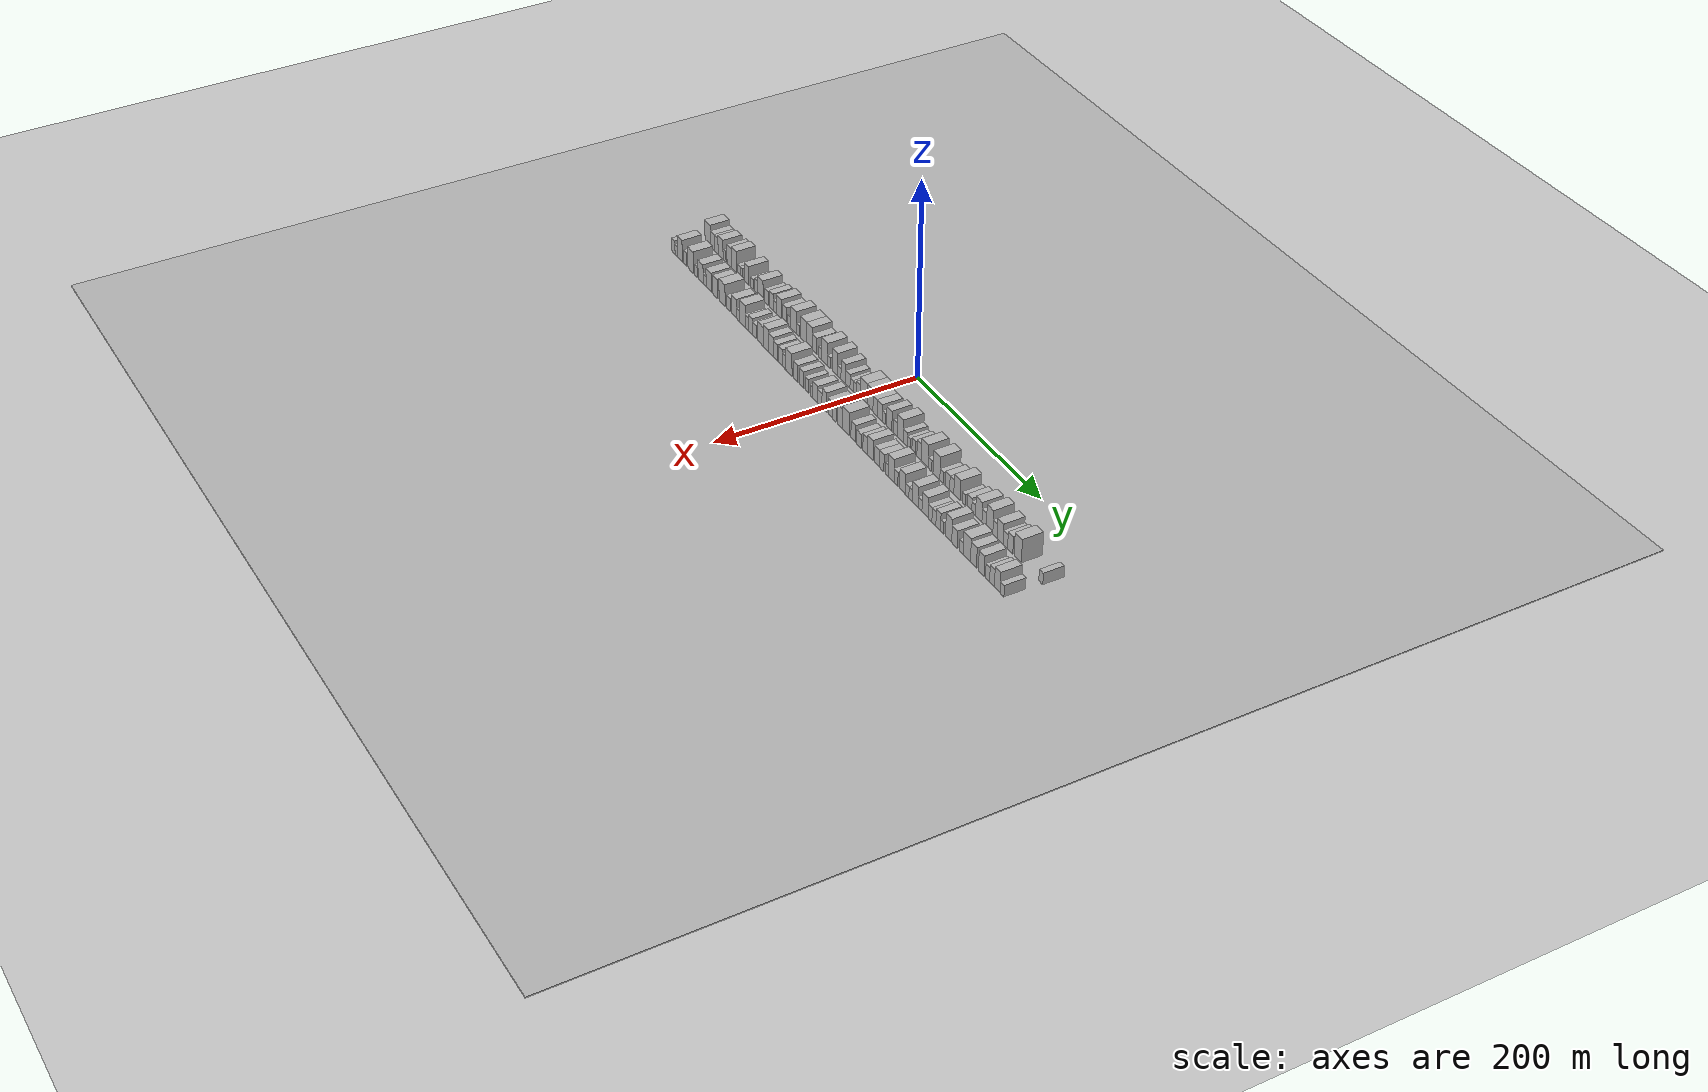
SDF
<?xml version="1.0" encoding="utf-8"?>

<sdf version="1.6">

   <world name="default">

      <gui fullscreen="0">

         <camera name="user_camera">

            <pose>-15 0 4.57585 0 0 0</pose>

            <view_controller>orbit</view_controller>

         </camera>

      </gui>

      <scene>

         <sky>

           <clouds>

             <speed>12</speed>

           </clouds>

         </sky>

         <ambient>0.4 0.4 0.4 1</ambient>

         <background>0.7 0.7 0.7 1</background>

         <shadows>1</shadows>

      </scene>

      <gravity>0 0 -9.8066</gravity>

      <magnetic_field>6e-06 2.3e-05 -4.2e-05</magnetic_field>

      <physics default="0" name="default_physics" type="ode">

         <ode>

            <solver>

               <type>quick</type>

               <iters>10</iters>

               <sor>1.0</sor>

               <use_dynamic_moi_rescaling>0</use_dynamic_moi_rescaling>

            </solver>

            <constraints>

               <cfm>0</cfm>

               <erp>0.2</erp>

               <contact_max_correcting_vel>100</contact_max_correcting_vel>

               <contact_surface_layer>0.001</contact_surface_layer>

            </constraints>

         </ode>

         <max_step_size>0.004</max_step_size>

         <real_time_factor>1</real_time_factor>

         <real_time_update_rate>250</real_time_update_rate>

      </physics>

      <light name="sun" type="directional">

         <cast_shadows>1</cast_shadows>

         <pose>0 0 10 0 0 0</pose>

         <diffuse>0.8 0.8 0.8 1</diffuse>

         <specular>0.2 0.2 0.2 1</specular>

         <attenuation>

            <range>1000</range>

            <constant>0.9</constant>

            <linear>0.01</linear>

            <quadratic>0.001</quadratic>

         </attenuation>

         <direction>-0.5 0.1 -0.9</direction>

      </light>

      <include>

         <name>ground_plane_1</name>

         <uri>model://HANNAS_ground_plane</uri>

         <pose>0 0 0  0 0 0</pose>

      </include>

      <include>

         <name>ground_plane_2</name>

         <uri>model://HANNAS_ground_plane</uri>

         <pose>100 0 0  0 0 0</pose>

      </include>

      <model name="building_1">

         <static>1</static>

         <pose frame="">50.0000 -282.1918 0 0.000000 0.000000 0.000000</pose>

         <link name="link">

            <pose frame="">0 0 12.00 0 0 0</pose>

            <collision name="collision">

               <geometry>

                  <box>

                     <size>20.0000 11.6164 24.0000</size>

                  </box>

               </geometry>

               <max_contacts>10</max_contacts>

               <surface>

                  <contact>

                     <ode/>

                  </contact>

                  <bounce/>

                  <friction>

                     <torsional>

                        <ode/>

                     </torsional>

                     <ode/>

                  </friction>

               </surface>

            </collision>

            <visual name="visual">

               <cast_shadows>0</cast_shadows>

               <geometry>

                  <box>

                     <size>20.0000 11.6164 24.0000</size>

                  </box>

               </geometry>

               <material>

                  <script>

                     <uri>model://HANNAS_wall/materials/scripts</uri>

                     <uri>model://HANNAS_wall/materials/textures</uri>

                     <name>vrc/HANNAS_wall</name>

                  </script>

               </material>

            </visual>

            <self_collide>0</self_collide>

            <enable_wind>0</enable_wind>

            <kinematic>0</kinematic>

         </link>

      </model>

      <model name="building_2">

         <static>1</static>

         <pose frame="">50.0000 -272.6289 0 0.000000 0.000000 0.000000</pose>

         <link name="link">

            <pose frame="">0 0 9.00 0 0 0</pose>

            <collision name="collision">

               <geometry>

                  <box>

                     <size>20.0000 7.5093 18.0000</size>

                  </box>

               </geometry>

               <max_contacts>10</max_contacts>

               <surface>

                  <contact>

                     <ode/>

                  </contact>

                  <bounce/>

                  <friction>

                     <torsional>

                        <ode/>

                     </torsional>

                     <ode/>

                  </friction>

               </surface>

            </collision>

            <visual name="visual">

               <cast_shadows>0</cast_shadows>

               <geometry>

                  <box>

                     <size>20.0000 7.5093 18.0000</size>

                  </box>

               </geometry>

               <material>

                  <script>

                     <uri>model://HANNAS_wall/materials/scripts</uri>

                     <uri>model://HANNAS_wall/materials/textures</uri>

                     <name>vrc/HANNAS_wall</name>

                  </script>

               </material>

            </visual>

            <self_collide>0</self_collide>

            <enable_wind>0</enable_wind>

            <kinematic>0</kinematic>

         </link>

      </model>

      <model name="building_3">

         <static>1</static>

         <pose frame="">50.0000 -265.1773 0 0.000000 0.000000 0.000000</pose>

         <link name="link">

            <pose frame="">0 0 9.00 0 0 0</pose>

            <collision name="collision">

               <geometry>

                  <box>

                     <size>20.0000 7.3941 18.0000</size>

                  </box>

               </geometry>

               <max_contacts>10</max_contacts>

               <surface>

                  <contact>

                     <ode/>

                  </contact>

                  <bounce/>

                  <friction>

                     <torsional>

                        <ode/>

                     </torsional>

                     <ode/>

                  </friction>

               </surface>

            </collision>

            <visual name="visual">

               <cast_shadows>0</cast_shadows>

               <geometry>

                  <box>

                     <size>20.0000 7.3941 18.0000</size>

                  </box>

               </geometry>

               <material>

                  <script>

                     <uri>model://HANNAS_wall/materials/scripts</uri>

                     <uri>model://HANNAS_wall/materials/textures</uri>

                     <name>vrc/HANNAS_wall</name>

                  </script>

               </material>

            </visual>

            <self_collide>0</self_collide>

            <enable_wind>0</enable_wind>

            <kinematic>0</kinematic>

         </link>

      </model>

      <model name="building_4">

         <static>1</static>

         <pose frame="">50.0000 -256.5117 0 0.000000 0.000000 0.000000</pose>

         <link name="link">

            <pose frame="">0 0 10.50 0 0 0</pose>

            <collision name="collision">

               <geometry>

                  <box>

                     <size>20.0000 9.9371 21.0000</size>

                  </box>

               </geometry>

               <max_contacts>10</max_contacts>

               <surface>

                  <contact>

                     <ode/>

                  </contact>

                  <bounce/>

                  <friction>

                     <torsional>

                        <ode/>

                     </torsional>

                     <ode/>

                  </friction>

               </surface>

            </collision>

            <visual name="visual">

               <cast_shadows>0</cast_shadows>

               <geometry>

                  <box>

                     <size>20.0000 9.9371 21.0000</size>

                  </box>

               </geometry>

               <material>

                  <script>

                     <uri>model://HANNAS_wall/materials/scripts</uri>

                     <uri>model://HANNAS_wall/materials/textures</uri>

                     <name>vrc/HANNAS_wall</name>

                  </script>

               </material>

            </visual>

            <self_collide>0</self_collide>

            <enable_wind>0</enable_wind>

            <kinematic>0</kinematic>

         </link>

      </model>

      <model name="building_5">

         <static>1</static>

         <pose frame="">50.0000 -248.6620 0 0.000000 0.000000 0.000000</pose>

         <link name="link">

            <pose frame="">0 0 6.00 0 0 0</pose>

            <collision name="collision">

               <geometry>

                  <box>

                     <size>20.0000 5.7622 12.0000</size>

                  </box>

               </geometry>

               <max_contacts>10</max_contacts>

               <surface>

                  <contact>

                     <ode/>

                  </contact>

                  <bounce/>

                  <friction>

                     <torsional>

                        <ode/>

                     </torsional>

                     <ode/>

                  </friction>

               </surface>

            </collision>

            <visual name="visual">

               <cast_shadows>0</cast_shadows>

               <geometry>

                  <box>

                     <size>20.0000 5.7622 12.0000</size>

                  </box>

               </geometry>

               <material>

                  <script>

                     <uri>model://HANNAS_wall/materials/scripts</uri>

                     <uri>model://HANNAS_wall/materials/textures</uri>

                     <name>vrc/HANNAS_wall</name>

                  </script>

               </material>

            </visual>

            <self_collide>0</self_collide>

            <enable_wind>0</enable_wind>

            <kinematic>0</kinematic>

         </link>

      </model>

      <model name="building_6">

         <static>1</static>

         <pose frame="">50.0000 -239.1442 0 0.000000 0.000000 0.000000</pose>

         <link name="link">

            <pose frame="">0 0 10.50 0 0 0</pose>

            <collision name="collision">

               <geometry>

                  <box>

                     <size>20.0000 9.2733 21.0000</size>

                  </box>

               </geometry>

               <max_contacts>10</max_contacts>

               <surface>

                  <contact>

                     <ode/>

                  </contact>

                  <bounce/>

                  <friction>

                     <torsional>

                        <ode/>

                     </torsional>

                     <ode/>

                  </friction>

               </surface>

            </collision>

            <visual name="visual">

               <cast_shadows>0</cast_shadows>

               <geometry>

                  <box>

                     <size>20.0000 9.2733 21.0000</size>

                  </box>

               </geometry>

               <material>

                  <script>

                     <uri>model://HANNAS_wall/materials/scripts</uri>

                     <uri>model://HANNAS_wall/materials/textures</uri>

                     <name>vrc/HANNAS_wall</name>

                  </script>

               </material>

            </visual>

            <self_collide>0</self_collide>

            <enable_wind>0</enable_wind>

            <kinematic>0</kinematic>

         </link>

      </model>

      <model name="building_7">

         <static>1</static>

         <pose frame="">50.0000 -229.4706 0 0.000000 0.000000 0.000000</pose>

         <link name="link">

            <pose frame="">0 0 12.00 0 0 0</pose>

            <collision name="collision">

               <geometry>

                  <box>

                     <size>20.0000 10.0738 24.0000</size>

                  </box>

               </geometry>

               <max_contacts>10</max_contacts>

               <surface>

                  <contact>

                     <ode/>

                  </contact>

                  <bounce/>

                  <friction>

                     <torsional>

                        <ode/>

                     </torsional>

                     <ode/>

                  </friction>

               </surface>

            </collision>

            <visual name="visual">

               <cast_shadows>0</cast_shadows>

               <geometry>

                  <box>

                     <size>20.0000 10.0738 24.0000</size>

                  </box>

               </geometry>

               <material>

                  <script>

                     <uri>model://HANNAS_wall/materials/scripts</uri>

                     <uri>model://HANNAS_wall/materials/textures</uri>

                     <name>vrc/HANNAS_wall</name>

                  </script>

               </material>

            </visual>

            <self_collide>0</self_collide>

            <enable_wind>0</enable_wind>

            <kinematic>0</kinematic>

         </link>

      </model>

      <model name="building_8">

         <static>1</static>

         <pose frame="">50.0000 -219.9659 0 0.000000 0.000000 0.000000</pose>

         <link name="link">

            <pose frame="">0 0 6.00 0 0 0</pose>

            <collision name="collision">

               <geometry>

                  <box>

                     <size>20.0000 4.9356 12.0000</size>

                  </box>

               </geometry>

               <max_contacts>10</max_contacts>

               <surface>

                  <contact>

                     <ode/>

                  </contact>

                  <bounce/>

                  <friction>

                     <torsional>

                        <ode/>

                     </torsional>

                     <ode/>

                  </friction>

               </surface>

            </collision>

            <visual name="visual">

               <cast_shadows>0</cast_shadows>

               <geometry>

                  <box>

                     <size>20.0000 4.9356 12.0000</size>

                  </box>

               </geometry>

               <material>

                  <script>

                     <uri>model://HANNAS_wall/materials/scripts</uri>

                     <uri>model://HANNAS_wall/materials/textures</uri>

                     <name>vrc/HANNAS_wall</name>

                  </script>

               </material>

            </visual>

            <self_collide>0</self_collide>

            <enable_wind>0</enable_wind>

            <kinematic>0</kinematic>

         </link>

      </model>

      <model name="building_9">

         <static>1</static>

         <pose frame="">50.0000 -214.8974 0 0.000000 0.000000 0.000000</pose>

         <link name="link">

            <pose frame="">0 0 6.00 0 0 0</pose>

            <collision name="collision">

               <geometry>

                  <box>

                     <size>20.0000 5.2013 12.0000</size>

                  </box>

               </geometry>

               <max_contacts>10</max_contacts>

               <surface>

                  <contact>

                     <ode/>

                  </contact>

                  <bounce/>

                  <friction>

                     <torsional>

                        <ode/>

                     </torsional>

                     <ode/>

                  </friction>

               </surface>

            </collision>

            <visual name="visual">

               <cast_shadows>0</cast_shadows>

               <geometry>

                  <box>

                     <size>20.0000 5.2013 12.0000</size>

                  </box>

               </geometry>

               <material>

                  <script>

                     <uri>model://HANNAS_wall/materials/scripts</uri>

                     <uri>model://HANNAS_wall/materials/textures</uri>

                     <name>vrc/HANNAS_wall</name>

                  </script>

               </material>

            </visual>

            <self_collide>0</self_collide>

            <enable_wind>0</enable_wind>

            <kinematic>0</kinematic>

         </link>

      </model>

      <model name="building_10">

         <static>1</static>

         <pose frame="">50.0000 -204.9406 0 0.000000 0.000000 0.000000</pose>

         <link name="link">

            <pose frame="">0 0 10.50 0 0 0</pose>

            <collision name="collision">

               <geometry>

                  <box>

                     <size>20.0000 8.7122 21.0000</size>

                  </box>

               </geometry>

               <max_contacts>10</max_contacts>

               <surface>

                  <contact>

                     <ode/>

                  </contact>

                  <bounce/>

                  <friction>

                     <torsional>

                        <ode/>

                     </torsional>

                     <ode/>

                  </friction>

               </surface>

            </collision>

            <visual name="visual">

               <cast_shadows>0</cast_shadows>

               <geometry>

                  <box>

                     <size>20.0000 8.7122 21.0000</size>

                  </box>

               </geometry>

               <material>

                  <script>

                     <uri>model://HANNAS_wall/materials/scripts</uri>

                     <uri>model://HANNAS_wall/materials/textures</uri>

                     <name>vrc/HANNAS_wall</name>

                  </script>

               </material>

            </visual>

            <self_collide>0</self_collide>

            <enable_wind>0</enable_wind>

            <kinematic>0</kinematic>

         </link>

      </model>

      <model name="building_11">

         <static>1</static>

         <pose frame="">50.0000 -194.9367 0 0.000000 0.000000 0.000000</pose>

         <link name="link">

            <pose frame="">0 0 6.00 0 0 0</pose>

            <collision name="collision">

               <geometry>

                  <box>

                     <size>20.0000 5.2956 12.0000</size>

                  </box>

               </geometry>

               <max_contacts>10</max_contacts>

               <surface>

                  <contact>

                     <ode/>

                  </contact>

                  <bounce/>

                  <friction>

                     <torsional>

                        <ode/>

                     </torsional>

                     <ode/>

                  </friction>

               </surface>

            </collision>

            <visual name="visual">

               <cast_shadows>0</cast_shadows>

               <geometry>

                  <box>

                     <size>20.0000 5.2956 12.0000</size>

                  </box>

               </geometry>

               <material>

                  <script>

                     <uri>model://HANNAS_wall/materials/scripts</uri>

                     <uri>model://HANNAS_wall/materials/textures</uri>

                     <name>vrc/HANNAS_wall</name>

                  </script>

               </material>

            </visual>

            <self_collide>0</self_collide>

            <enable_wind>0</enable_wind>

            <kinematic>0</kinematic>

         </link>

      </model>

      <model name="building_12">

         <static>1</static>

         <pose frame="">50.0000 -186.1868 0 0.000000 0.000000 0.000000</pose>

         <link name="link">

            <pose frame="">0 0 7.50 0 0 0</pose>

            <collision name="collision">

               <geometry>

                  <box>

                     <size>20.0000 6.2042 15.0000</size>

                  </box>

               </geometry>

               <max_contacts>10</max_contacts>

               <surface>

                  <contact>

                     <ode/>

                  </contact>

                  <bounce/>

                  <friction>

                     <torsional>

                        <ode/>

                     </torsional>

                     <ode/>

                  </friction>

               </surface>

            </collision>

            <visual name="visual">

               <cast_shadows>0</cast_shadows>

               <geometry>

                  <box>

                     <size>20.0000 6.2042 15.0000</size>

                  </box>

               </geometry>

               <material>

                  <script>

                     <uri>model://HANNAS_wall/materials/scripts</uri>

                     <uri>model://HANNAS_wall/materials/textures</uri>

                     <name>vrc/HANNAS_wall</name>

                  </script>

               </material>

            </visual>

            <self_collide>0</self_collide>

            <enable_wind>0</enable_wind>

            <kinematic>0</kinematic>

         </link>

      </model>

      <model name="building_13">

         <static>1</static>

         <pose frame="">50.0000 -178.1175 0 0.000000 0.000000 0.000000</pose>

         <link name="link">

            <pose frame="">0 0 10.50 0 0 0</pose>

            <collision name="collision">

               <geometry>

                  <box>

                     <size>20.0000 9.9345 21.0000</size>

                  </box>

               </geometry>

               <max_contacts>10</max_contacts>

               <surface>

                  <contact>

                     <ode/>

                  </contact>

                  <bounce/>

                  <friction>

                     <torsional>

                        <ode/>

                     </torsional>

                     <ode/>

                  </friction>

               </surface>

            </collision>

            <visual name="visual">

               <cast_shadows>0</cast_shadows>

               <geometry>

                  <box>

                     <size>20.0000 9.9345 21.0000</size>

                  </box>

               </geometry>

               <material>

                  <script>

                     <uri>model://HANNAS_wall/materials/scripts</uri>

                     <uri>model://HANNAS_wall/materials/textures</uri>

                     <name>vrc/HANNAS_wall</name>

                  </script>

               </material>

            </visual>

            <self_collide>0</self_collide>

            <enable_wind>0</enable_wind>

            <kinematic>0</kinematic>

         </link>

      </model>

      <model name="building_14">

         <static>1</static>

         <pose frame="">50.0000 -166.7029 0 0.000000 0.000000 0.000000</pose>

         <link name="link">

            <pose frame="">0 0 7.50 0 0 0</pose>

            <collision name="collision">

               <geometry>

                  <box>

                     <size>20.0000 6.8947 15.0000</size>

                  </box>

               </geometry>

               <max_contacts>10</max_contacts>

               <surface>

                  <contact>

                     <ode/>

                  </contact>

                  <bounce/>

                  <friction>

                     <torsional>

                        <ode/>

                     </torsional>

                     <ode/>

                  </friction>

               </surface>

            </collision>

            <visual name="visual">

               <cast_shadows>0</cast_shadows>

               <geometry>

                  <box>

                     <size>20.0000 6.8947 15.0000</size>

                  </box>

               </geometry>

               <material>

                  <script>

                     <uri>model://HANNAS_wall/materials/scripts</uri>

                     <uri>model://HANNAS_wall/materials/textures</uri>

                     <name>vrc/HANNAS_wall</name>

                  </script>

               </material>

            </visual>

            <self_collide>0</self_collide>

            <enable_wind>0</enable_wind>

            <kinematic>0</kinematic>

         </link>

      </model>

      <model name="building_15">

         <static>1</static>

         <pose frame="">50.0000 -157.5262 0 0.000000 0.000000 0.000000</pose>

         <link name="link">

            <pose frame="">0 0 9.00 0 0 0</pose>

            <collision name="collision">

               <geometry>

                  <box>

                     <size>20.0000 7.4588 18.0000</size>

                  </box>

               </geometry>

               <max_contacts>10</max_contacts>

               <surface>

                  <contact>

                     <ode/>

                  </contact>

                  <bounce/>

                  <friction>

                     <torsional>

                        <ode/>

                     </torsional>

                     <ode/>

                  </friction>

               </surface>

            </collision>

            <visual name="visual">

               <cast_shadows>0</cast_shadows>

               <geometry>

                  <box>

                     <size>20.0000 7.4588 18.0000</size>

                  </box>

               </geometry>

               <material>

                  <script>

                     <uri>model://HANNAS_wall/materials/scripts</uri>

                     <uri>model://HANNAS_wall/materials/textures</uri>

                     <name>vrc/HANNAS_wall</name>

                  </script>

               </material>

            </visual>

            <self_collide>0</self_collide>

            <enable_wind>0</enable_wind>

            <kinematic>0</kinematic>

         </link>

      </model>

      <model name="building_16">

         <static>1</static>

         <pose frame="">50.0000 -151.0587 0 0.000000 0.000000 0.000000</pose>

         <link name="link">

            <pose frame="">0 0 6.00 0 0 0</pose>

            <collision name="collision">

               <geometry>

                  <box>

                     <size>20.0000 5.4762 12.0000</size>

                  </box>

               </geometry>

               <max_contacts>10</max_contacts>

               <surface>

                  <contact>

                     <ode/>

                  </contact>

                  <bounce/>

                  <friction>

                     <torsional>

                        <ode/>

                     </torsional>

                     <ode/>

                  </friction>

               </surface>

            </collision>

            <visual name="visual">

               <cast_shadows>0</cast_shadows>

               <geometry>

                  <box>

                     <size>20.0000 5.4762 12.0000</size>

                  </box>

               </geometry>

               <material>

                  <script>

                     <uri>model://HANNAS_wall/materials/scripts</uri>

                     <uri>model://HANNAS_wall/materials/textures</uri>

                     <name>vrc/HANNAS_wall</name>

                  </script>

               </material>

            </visual>

            <self_collide>0</self_collide>

            <enable_wind>0</enable_wind>

            <kinematic>0</kinematic>

         </link>

      </model>

      <model name="building_17">

         <static>1</static>

         <pose frame="">50.0000 -143.1364 0 0.000000 0.000000 0.000000</pose>

         <link name="link">

            <pose frame="">0 0 10.50 0 0 0</pose>

            <collision name="collision">

               <geometry>

                  <box>

                     <size>20.0000 10.3685 21.0000</size>

                  </box>

               </geometry>

               <max_contacts>10</max_contacts>

               <surface>

                  <contact>

                     <ode/>

                  </contact>

                  <bounce/>

                  <friction>

                     <torsional>

                        <ode/>

                     </torsional>

                     <ode/>

                  </friction>

               </surface>

            </collision>

            <visual name="visual">

               <cast_shadows>0</cast_shadows>

               <geometry>

                  <box>

                     <size>20.0000 10.3685 21.0000</size>

                  </box>

               </geometry>

               <material>

                  <script>

                     <uri>model://HANNAS_wall/materials/scripts</uri>

                     <uri>model://HANNAS_wall/materials/textures</uri>

                     <name>vrc/HANNAS_wall</name>

                  </script>

               </material>

            </visual>

            <self_collide>0</self_collide>

            <enable_wind>0</enable_wind>

            <kinematic>0</kinematic>

         </link>

      </model>

      <model name="building_18">

         <static>1</static>

         <pose frame="">50.0000 -132.0665 0 0.000000 0.000000 0.000000</pose>

         <link name="link">

            <pose frame="">0 0 9.00 0 0 0</pose>

            <collision name="collision">

               <geometry>

                  <box>

                     <size>20.0000 7.7713 18.0000</size>

                  </box>

               </geometry>

               <max_contacts>10</max_contacts>

               <surface>

                  <contact>

                     <ode/>

                  </contact>

                  <bounce/>

                  <friction>

                     <torsional>

                        <ode/>

                     </torsional>

                     <ode/>

                  </friction>

               </surface>

            </collision>

            <visual name="visual">

               <cast_shadows>0</cast_shadows>

               <geometry>

                  <box>

                     <size>20.0000 7.7713 18.0000</size>

                  </box>

               </geometry>

               <material>

                  <script>

                     <uri>model://HANNAS_wall/materials/scripts</uri>

                     <uri>model://HANNAS_wall/materials/textures</uri>

                     <name>vrc/HANNAS_wall</name>

                  </script>

               </material>

            </visual>

            <self_collide>0</self_collide>

            <enable_wind>0</enable_wind>

            <kinematic>0</kinematic>

         </link>

      </model>

      <model name="building_19">

         <static>1</static>

         <pose frame="">50.0000 -123.4690 0 0.000000 0.000000 0.000000</pose>

         <link name="link">

            <pose frame="">0 0 6.00 0 0 0</pose>

            <collision name="collision">

               <geometry>

                  <box>

                     <size>20.0000 5.4237 12.0000</size>

                  </box>

               </geometry>

               <max_contacts>10</max_contacts>

               <surface>

                  <contact>

                     <ode/>

                  </contact>

                  <bounce/>

                  <friction>

                     <torsional>

                        <ode/>

                     </torsional>

                     <ode/>

                  </friction>

               </surface>

            </collision>

            <visual name="visual">

               <cast_shadows>0</cast_shadows>

               <geometry>

                  <box>

                     <size>20.0000 5.4237 12.0000</size>

                  </box>

               </geometry>

               <material>

                  <script>

                     <uri>model://HANNAS_wall/materials/scripts</uri>

                     <uri>model://HANNAS_wall/materials/textures</uri>

                     <name>vrc/HANNAS_wall</name>

                  </script>

               </material>

            </visual>

            <self_collide>0</self_collide>

            <enable_wind>0</enable_wind>

            <kinematic>0</kinematic>

         </link>

      </model>

      <model name="building_20">

         <static>1</static>

         <pose frame="">50.0000 -115.5682 0 0.000000 0.000000 0.000000</pose>

         <link name="link">

            <pose frame="">0 0 12.00 0 0 0</pose>

            <collision name="collision">

               <geometry>

                  <box>

                     <size>20.0000 10.3779 24.0000</size>

                  </box>

               </geometry>

               <max_contacts>10</max_contacts>

               <surface>

                  <contact>

                     <ode/>

                  </contact>

                  <bounce/>

                  <friction>

                     <torsional>

                        <ode/>

                     </torsional>

                     <ode/>

                  </friction>

               </surface>

            </collision>

            <visual name="visual">

               <cast_shadows>0</cast_shadows>

               <geometry>

                  <box>

                     <size>20.0000 10.3779 24.0000</size>

                  </box>

               </geometry>

               <material>

                  <script>

                     <uri>model://HANNAS_wall/materials/scripts</uri>

                     <uri>model://HANNAS_wall/materials/textures</uri>

                     <name>vrc/HANNAS_wall</name>

                  </script>

               </material>

            </visual>

            <self_collide>0</self_collide>

            <enable_wind>0</enable_wind>

            <kinematic>0</kinematic>

         </link>

      </model>

      <model name="building_21">

         <static>1</static>

         <pose frame="">50.0000 -107.8288 0 0.000000 0.000000 0.000000</pose>

         <link name="link">

            <pose frame="">0 0 6.00 0 0 0</pose>

            <collision name="collision">

               <geometry>

                  <box>

                     <size>20.0000 5.1009 12.0000</size>

                  </box>

               </geometry>

               <max_contacts>10</max_contacts>

               <surface>

                  <contact>

                     <ode/>

                  </contact>

                  <bounce/>

                  <friction>

                     <torsional>

                        <ode/>

                     </torsional>

                     <ode/>

                  </friction>

               </surface>

            </collision>

            <visual name="visual">

               <cast_shadows>0</cast_shadows>

               <geometry>

                  <box>

                     <size>20.0000 5.1009 12.0000</size>

                  </box>

               </geometry>

               <material>

                  <script>

                     <uri>model://HANNAS_wall/materials/scripts</uri>

                     <uri>model://HANNAS_wall/materials/textures</uri>

                     <name>vrc/HANNAS_wall</name>

                  </script>

               </material>

            </visual>

            <self_collide>0</self_collide>

            <enable_wind>0</enable_wind>

            <kinematic>0</kinematic>

         </link>

      </model>

      <model name="building_22">

         <static>1</static>

         <pose frame="">50.0000 -97.4031 0 0.000000 0.000000 0.000000</pose>

         <link name="link">

            <pose frame="">0 0 12.00 0 0 0</pose>

            <collision name="collision">

               <geometry>

                  <box>

                     <size>20.0000 11.7504 24.0000</size>

                  </box>

               </geometry>

               <max_contacts>10</max_contacts>

               <surface>

                  <contact>

                     <ode/>

                  </contact>

                  <bounce/>

                  <friction>

                     <torsional>

                        <ode/>

                     </torsional>

                     <ode/>

                  </friction>

               </surface>

            </collision>

            <visual name="visual">

               <cast_shadows>0</cast_shadows>

               <geometry>

                  <box>

                     <size>20.0000 11.7504 24.0000</size>

                  </box>

               </geometry>

               <material>

                  <script>

                     <uri>model://HANNAS_wall/materials/scripts</uri>

                     <uri>model://HANNAS_wall/materials/textures</uri>

                     <name>vrc/HANNAS_wall</name>

                  </script>

               </material>

            </visual>

            <self_collide>0</self_collide>

            <enable_wind>0</enable_wind>

            <kinematic>0</kinematic>

         </link>

      </model>

      <model name="building_23">

         <static>1</static>

         <pose frame="">50.0000 -86.3627 0 0.000000 0.000000 0.000000</pose>

         <link name="link">

            <pose frame="">0 0 12.00 0 0 0</pose>

            <collision name="collision">

               <geometry>

                  <box>

                     <size>20.0000 10.3305 24.0000</size>

                  </box>

               </geometry>

               <max_contacts>10</max_contacts>

               <surface>

                  <contact>

                     <ode/>

                  </contact>

                  <bounce/>

                  <friction>

                     <torsional>

                        <ode/>

                     </torsional>

                     <ode/>

                  </friction>

               </surface>

            </collision>

            <visual name="visual">

               <cast_shadows>0</cast_shadows>

               <geometry>

                  <box>

                     <size>20.0000 10.3305 24.0000</size>

                  </box>

               </geometry>

               <material>

                  <script>

                     <uri>model://HANNAS_wall/materials/scripts</uri>

                     <uri>model://HANNAS_wall/materials/textures</uri>

                     <name>vrc/HANNAS_wall</name>

                  </script>

               </material>

            </visual>

            <self_collide>0</self_collide>

            <enable_wind>0</enable_wind>

            <kinematic>0</kinematic>

         </link>

      </model>

      <model name="building_24">

         <static>1</static>

         <pose frame="">50.0000 -76.9648 0 0.000000 0.000000 0.000000</pose>

         <link name="link">

            <pose frame="">0 0 9.00 0 0 0</pose>

            <collision name="collision">

               <geometry>

                  <box>

                     <size>20.0000 8.4652 18.0000</size>

                  </box>

               </geometry>

               <max_contacts>10</max_contacts>

               <surface>

                  <contact>

                     <ode/>

                  </contact>

                  <bounce/>

                  <friction>

                     <torsional>

                        <ode/>

                     </torsional>

                     <ode/>

                  </friction>

               </surface>

            </collision>

            <visual name="visual">

               <cast_shadows>0</cast_shadows>

               <geometry>

                  <box>

                     <size>20.0000 8.4652 18.0000</size>

                  </box>

               </geometry>

               <material>

                  <script>

                     <uri>model://HANNAS_wall/materials/scripts</uri>

                     <uri>model://HANNAS_wall/materials/textures</uri>

                     <name>vrc/HANNAS_wall</name>

                  </script>

               </material>

            </visual>

            <self_collide>0</self_collide>

            <enable_wind>0</enable_wind>

            <kinematic>0</kinematic>

         </link>

      </model>

      <model name="building_25">

         <static>1</static>

         <pose frame="">50.0000 -66.9805 0 0.000000 0.000000 0.000000</pose>

         <link name="link">

            <pose frame="">0 0 6.00 0 0 0</pose>

            <collision name="collision">

               <geometry>

                  <box>

                     <size>20.0000 5.5034 12.0000</size>

                  </box>

               </geometry>

               <max_contacts>10</max_contacts>

               <surface>

                  <contact>

                     <ode/>

                  </contact>

                  <bounce/>

                  <friction>

                     <torsional>

                        <ode/>

                     </torsional>

                     <ode/>

                  </friction>

               </surface>

            </collision>

            <visual name="visual">

               <cast_shadows>0</cast_shadows>

               <geometry>

                  <box>

                     <size>20.0000 5.5034 12.0000</size>

                  </box>

               </geometry>

               <material>

                  <script>

                     <uri>model://HANNAS_wall/materials/scripts</uri>

                     <uri>model://HANNAS_wall/materials/textures</uri>

                     <name>vrc/HANNAS_wall</name>

                  </script>

               </material>

            </visual>

            <self_collide>0</self_collide>

            <enable_wind>0</enable_wind>

            <kinematic>0</kinematic>

         </link>

      </model>

      <model name="building_26">

         <static>1</static>

         <pose frame="">50.0000 -58.7749 0 0.000000 0.000000 0.000000</pose>

         <link name="link">

            <pose frame="">0 0 12.00 0 0 0</pose>

            <collision name="collision">

               <geometry>

                  <box>

                     <size>20.0000 10.9078 24.0000</size>

                  </box>

               </geometry>

               <max_contacts>10</max_contacts>

               <surface>

                  <contact>

                     <ode/>

                  </contact>

                  <bounce/>

                  <friction>

                     <torsional>

                        <ode/>

                     </torsional>

                     <ode/>

                  </friction>

               </surface>

            </collision>

            <visual name="visual">

               <cast_shadows>0</cast_shadows>

               <geometry>

                  <box>

                     <size>20.0000 10.9078 24.0000</size>

                  </box>

               </geometry>

               <material>

                  <script>

                     <uri>model://HANNAS_wall/materials/scripts</uri>

                     <uri>model://HANNAS_wall/materials/textures</uri>

                     <name>vrc/HANNAS_wall</name>

                  </script>

               </material>

            </visual>

            <self_collide>0</self_collide>

            <enable_wind>0</enable_wind>

            <kinematic>0</kinematic>

         </link>

      </model>

      <model name="building_27">

         <static>1</static>

         <pose frame="">50.0000 -50.8894 0 0.000000 0.000000 0.000000</pose>

         <link name="link">

            <pose frame="">0 0 6.00 0 0 0</pose>

            <collision name="collision">

               <geometry>

                  <box>

                     <size>20.0000 4.8633 12.0000</size>

                  </box>

               </geometry>

               <max_contacts>10</max_contacts>

               <surface>

                  <contact>

                     <ode/>

                  </contact>

                  <bounce/>

                  <friction>

                     <torsional>

                        <ode/>

                     </torsional>

                     <ode/>

                  </friction>

               </surface>

            </collision>

            <visual name="visual">

               <cast_shadows>0</cast_shadows>

               <geometry>

                  <box>

                     <size>20.0000 4.8633 12.0000</size>

                  </box>

               </geometry>

               <material>

                  <script>

                     <uri>model://HANNAS_wall/materials/scripts</uri>

                     <uri>model://HANNAS_wall/materials/textures</uri>

                     <name>vrc/HANNAS_wall</name>

                  </script>

               </material>

            </visual>

            <self_collide>0</self_collide>

            <enable_wind>0</enable_wind>

            <kinematic>0</kinematic>

         </link>

      </model>

      <model name="building_28">

         <static>1</static>

         <pose frame="">50.0000 -40.4735 0 0.000000 0.000000 0.000000</pose>

         <link name="link">

            <pose frame="">0 0 12.00 0 0 0</pose>

            <collision name="collision">

               <geometry>

                  <box>

                     <size>20.0000 9.9685 24.0000</size>

                  </box>

               </geometry>

               <max_contacts>10</max_contacts>

               <surface>

                  <contact>

                     <ode/>

                  </contact>

                  <bounce/>

                  <friction>

                     <torsional>

                        <ode/>

                     </torsional>

                     <ode/>

                  </friction>

               </surface>

            </collision>

            <visual name="visual">

               <cast_shadows>0</cast_shadows>

               <geometry>

                  <box>

                     <size>20.0000 9.9685 24.0000</size>

                  </box>

               </geometry>

               <material>

                  <script>

                     <uri>model://HANNAS_wall/materials/scripts</uri>

                     <uri>model://HANNAS_wall/materials/textures</uri>

                     <name>vrc/HANNAS_wall</name>

                  </script>

               </material>

            </visual>

            <self_collide>0</self_collide>

            <enable_wind>0</enable_wind>

            <kinematic>0</kinematic>

         </link>

      </model>

      <model name="building_29">

         <static>1</static>

         <pose frame="">50.0000 -32.5656 0 0.000000 0.000000 0.000000</pose>

         <link name="link">

            <pose frame="">0 0 6.00 0 0 0</pose>

            <collision name="collision">

               <geometry>

                  <box>

                     <size>20.0000 5.8473 12.0000</size>

                  </box>

               </geometry>

               <max_contacts>10</max_contacts>

               <surface>

                  <contact>

                     <ode/>

                  </contact>

                  <bounce/>

                  <friction>

                     <torsional>

                        <ode/>

                     </torsional>

                     <ode/>

                  </friction>

               </surface>

            </collision>

            <visual name="visual">

               <cast_shadows>0</cast_shadows>

               <geometry>

                  <box>

                     <size>20.0000 5.8473 12.0000</size>

                  </box>

               </geometry>

               <material>

                  <script>

                     <uri>model://HANNAS_wall/materials/scripts</uri>

                     <uri>model://HANNAS_wall/materials/textures</uri>

                     <name>vrc/HANNAS_wall</name>

                  </script>

               </material>

            </visual>

            <self_collide>0</self_collide>

            <enable_wind>0</enable_wind>

            <kinematic>0</kinematic>

         </link>

      </model>

      <model name="building_30">

         <static>1</static>

         <pose frame="">50.0000 -25.3469 0 0.000000 0.000000 0.000000</pose>

         <link name="link">

            <pose frame="">0 0 10.50 0 0 0</pose>

            <collision name="collision">

               <geometry>

                  <box>

                     <size>20.0000 8.5902 21.0000</size>

                  </box>

               </geometry>

               <max_contacts>10</max_contacts>

               <surface>

                  <contact>

                     <ode/>

                  </contact>

                  <bounce/>

                  <friction>

                     <torsional>

                        <ode/>

                     </torsional>

                     <ode/>

                  </friction>

               </surface>

            </collision>

            <visual name="visual">

               <cast_shadows>0</cast_shadows>

               <geometry>

                  <box>

                     <size>20.0000 8.5902 21.0000</size>

                  </box>

               </geometry>

               <material>

                  <script>

                     <uri>model://HANNAS_wall/materials/scripts</uri>

                     <uri>model://HANNAS_wall/materials/textures</uri>

                     <name>vrc/HANNAS_wall</name>

                  </script>

               </material>

            </visual>

            <self_collide>0</self_collide>

            <enable_wind>0</enable_wind>

            <kinematic>0</kinematic>

         </link>

      </model>

      <model name="building_31">

         <static>1</static>

         <pose frame="">50.0000 -17.3858 0 0.000000 0.000000 0.000000</pose>

         <link name="link">

            <pose frame="">0 0 7.50 0 0 0</pose>

            <collision name="collision">

               <geometry>

                  <box>

                     <size>20.0000 7.3321 15.0000</size>

                  </box>

               </geometry>

               <max_contacts>10</max_contacts>

               <surface>

                  <contact>

                     <ode/>

                  </contact>

                  <bounce/>

                  <friction>

                     <torsional>

                        <ode/>

                     </torsional>

                     <ode/>

                  </friction>

               </surface>

            </collision>

            <visual name="visual">

               <cast_shadows>0</cast_shadows>

               <geometry>

                  <box>

                     <size>20.0000 7.3321 15.0000</size>

                  </box>

               </geometry>

               <material>

                  <script>

                     <uri>model://HANNAS_wall/materials/scripts</uri>

                     <uri>model://HANNAS_wall/materials/textures</uri>

                     <name>vrc/HANNAS_wall</name>

                  </script>

               </material>

            </visual>

            <self_collide>0</self_collide>

            <enable_wind>0</enable_wind>

            <kinematic>0</kinematic>

         </link>

      </model>

      <model name="building_32">

         <static>1</static>

         <pose frame="">50.0000 -10.9680 0 0.000000 0.000000 0.000000</pose>

         <link name="link">

            <pose frame="">0 0 6.00 0 0 0</pose>

            <collision name="collision">

               <geometry>

                  <box>

                     <size>20.0000 5.5035 12.0000</size>

                  </box>

               </geometry>

               <max_contacts>10</max_contacts>

               <surface>

                  <contact>

                     <ode/>

                  </contact>

                  <bounce/>

                  <friction>

                     <torsional>

                        <ode/>

                     </torsional>

                     <ode/>

                  </friction>

               </surface>

            </collision>

            <visual name="visual">

               <cast_shadows>0</cast_shadows>

               <geometry>

                  <box>

                     <size>20.0000 5.5035 12.0000</size>

                  </box>

               </geometry>

               <material>

                  <script>

                     <uri>model://HANNAS_wall/materials/scripts</uri>

                     <uri>model://HANNAS_wall/materials/textures</uri>

                     <name>vrc/HANNAS_wall</name>

                  </script>

               </material>

            </visual>

            <self_collide>0</self_collide>

            <enable_wind>0</enable_wind>

            <kinematic>0</kinematic>

         </link>

      </model>

      <model name="building_33">

         <static>1</static>

         <pose frame="">50.0000 -5.3943 0 0.000000 0.000000 0.000000</pose>

         <link name="link">

            <pose frame="">0 0 6.00 0 0 0</pose>

            <collision name="collision">

               <geometry>

                  <box>

                     <size>20.0000 5.6439 12.0000</size>

                  </box>

               </geometry>

               <max_contacts>10</max_contacts>

               <surface>

                  <contact>

                     <ode/>

                  </contact>

                  <bounce/>

                  <friction>

                     <torsional>

                        <ode/>

                     </torsional>

                     <ode/>

                  </friction>

               </surface>

            </collision>

            <visual name="visual">

               <cast_shadows>0</cast_shadows>

               <geometry>

                  <box>

                     <size>20.0000 5.6439 12.0000</size>

                  </box>

               </geometry>

               <material>

                  <script>

                     <uri>model://HANNAS_wall/materials/scripts</uri>

                     <uri>model://HANNAS_wall/materials/textures</uri>

                     <name>vrc/HANNAS_wall</name>

                  </script>

               </material>

            </visual>

            <self_collide>0</self_collide>

            <enable_wind>0</enable_wind>

            <kinematic>0</kinematic>

         </link>

      </model>

      <model name="building_34">

         <static>1</static>

         <pose frame="">50.0000 0.9988 0 0.000000 0.000000 0.000000</pose>

         <link name="link">

            <pose frame="">0 0 7.50 0 0 0</pose>

            <collision name="collision">

               <geometry>

                  <box>

                     <size>20.0000 7.1422 15.0000</size>

                  </box>

               </geometry>

               <max_contacts>10</max_contacts>

               <surface>

                  <contact>

                     <ode/>

                  </contact>

                  <bounce/>

                  <friction>

                     <torsional>

                        <ode/>

                     </torsional>

                     <ode/>

                  </friction>

               </surface>

            </collision>

            <visual name="visual">

               <cast_shadows>0</cast_shadows>

               <geometry>

                  <box>

                     <size>20.0000 7.1422 15.0000</size>

                  </box>

               </geometry>

               <material>

                  <script>

                     <uri>model://HANNAS_wall/materials/scripts</uri>

                     <uri>model://HANNAS_wall/materials/textures</uri>

                     <name>vrc/HANNAS_wall</name>

                  </script>

               </material>

            </visual>

            <self_collide>0</self_collide>

            <enable_wind>0</enable_wind>

            <kinematic>0</kinematic>

         </link>

      </model>

      <model name="building_35">

         <static>1</static>

         <pose frame="">50.0000 10.4625 0 0.000000 0.000000 0.000000</pose>

         <link name="link">

            <pose frame="">0 0 12.00 0 0 0</pose>

            <collision name="collision">

               <geometry>

                  <box>

                     <size>20.0000 11.7853 24.0000</size>

                  </box>

               </geometry>

               <max_contacts>10</max_contacts>

               <surface>

                  <contact>

                     <ode/>

                  </contact>

                  <bounce/>

                  <friction>

                     <torsional>

                        <ode/>

                     </torsional>

                     <ode/>

                  </friction>

               </surface>

            </collision>

            <visual name="visual">

               <cast_shadows>0</cast_shadows>

               <geometry>

                  <box>

                     <size>20.0000 11.7853 24.0000</size>

                  </box>

               </geometry>

               <material>

                  <script>

                     <uri>model://HANNAS_wall/materials/scripts</uri>

                     <uri>model://HANNAS_wall/materials/textures</uri>

                     <name>vrc/HANNAS_wall</name>

                  </script>

               </material>

            </visual>

            <self_collide>0</self_collide>

            <enable_wind>0</enable_wind>

            <kinematic>0</kinematic>

         </link>

      </model>

      <model name="building_36">

         <static>1</static>

         <pose frame="">50.0000 21.2735 0 0.000000 0.000000 0.000000</pose>

         <link name="link">

            <pose frame="">0 0 12.00 0 0 0</pose>

            <collision name="collision">

               <geometry>

                  <box>

                     <size>20.0000 9.8368 24.0000</size>

                  </box>

               </geometry>

               <max_contacts>10</max_contacts>

               <surface>

                  <contact>

                     <ode/>

                  </contact>

                  <bounce/>

                  <friction>

                     <torsional>

                        <ode/>

                     </torsional>

                     <ode/>

                  </friction>

               </surface>

            </collision>

            <visual name="visual">

               <cast_shadows>0</cast_shadows>

               <geometry>

                  <box>

                     <size>20.0000 9.8368 24.0000</size>

                  </box>

               </geometry>

               <material>

                  <script>

                     <uri>model://HANNAS_wall/materials/scripts</uri>

                     <uri>model://HANNAS_wall/materials/textures</uri>

                     <name>vrc/HANNAS_wall</name>

                  </script>

               </material>

            </visual>

            <self_collide>0</self_collide>

            <enable_wind>0</enable_wind>

            <kinematic>0</kinematic>

         </link>

      </model>

      <model name="building_37">

         <static>1</static>

         <pose frame="">50.0000 30.0044 0 0.000000 0.000000 0.000000</pose>

         <link name="link">

            <pose frame="">0 0 9.00 0 0 0</pose>

            <collision name="collision">

               <geometry>

                  <box>

                     <size>20.0000 7.6249 18.0000</size>

                  </box>

               </geometry>

               <max_contacts>10</max_contacts>

               <surface>

                  <contact>

                     <ode/>

                  </contact>

                  <bounce/>

                  <friction>

                     <torsional>

                        <ode/>

                     </torsional>

                     <ode/>

                  </friction>

               </surface>

            </collision>

            <visual name="visual">

               <cast_shadows>0</cast_shadows>

               <geometry>

                  <box>

                     <size>20.0000 7.6249 18.0000</size>

                  </box>

               </geometry>

               <material>

                  <script>

                     <uri>model://HANNAS_wall/materials/scripts</uri>

                     <uri>model://HANNAS_wall/materials/textures</uri>

                     <name>vrc/HANNAS_wall</name>

                  </script>

               </material>

            </visual>

            <self_collide>0</self_collide>

            <enable_wind>0</enable_wind>

            <kinematic>0</kinematic>

         </link>

      </model>

      <model name="building_38">

         <static>1</static>

         <pose frame="">50.0000 38.2437 0 0.000000 0.000000 0.000000</pose>

         <link name="link">

            <pose frame="">0 0 9.00 0 0 0</pose>

            <collision name="collision">

               <geometry>

                  <box>

                     <size>20.0000 8.8538 18.0000</size>

                  </box>

               </geometry>

               <max_contacts>10</max_contacts>

               <surface>

                  <contact>

                     <ode/>

                  </contact>

                  <bounce/>

                  <friction>

                     <torsional>

                        <ode/>

                     </torsional>

                     <ode/>

                  </friction>

               </surface>

            </collision>

            <visual name="visual">

               <cast_shadows>0</cast_shadows>

               <geometry>

                  <box>

                     <size>20.0000 8.8538 18.0000</size>

                  </box>

               </geometry>

               <material>

                  <script>

                     <uri>model://HANNAS_wall/materials/scripts</uri>

                     <uri>model://HANNAS_wall/materials/textures</uri>

                     <name>vrc/HANNAS_wall</name>

                  </script>

               </material>

            </visual>

            <self_collide>0</self_collide>

            <enable_wind>0</enable_wind>

            <kinematic>0</kinematic>

         </link>

      </model>

      <model name="building_39">

         <static>1</static>

         <pose frame="">50.0000 45.1962 0 0.000000 0.000000 0.000000</pose>

         <link name="link">

            <pose frame="">0 0 6.00 0 0 0</pose>

            <collision name="collision">

               <geometry>

                  <box>

                     <size>20.0000 5.0511 12.0000</size>

                  </box>

               </geometry>

               <max_contacts>10</max_contacts>

               <surface>

                  <contact>

                     <ode/>

                  </contact>

                  <bounce/>

                  <friction>

                     <torsional>

                        <ode/>

                     </torsional>

                     <ode/>

                  </friction>

               </surface>

            </collision>

            <visual name="visual">

               <cast_shadows>0</cast_shadows>

               <geometry>

                  <box>

                     <size>20.0000 5.0511 12.0000</size>

                  </box>

               </geometry>

               <material>

                  <script>

                     <uri>model://HANNAS_wall/materials/scripts</uri>

                     <uri>model://HANNAS_wall/materials/textures</uri>

                     <name>vrc/HANNAS_wall</name>

                  </script>

               </material>

            </visual>

            <self_collide>0</self_collide>

            <enable_wind>0</enable_wind>

            <kinematic>0</kinematic>

         </link>

      </model>

      <model name="building_40">

         <static>1</static>

         <pose frame="">50.0000 54.0515 0 0.000000 0.000000 0.000000</pose>

         <link name="link">

            <pose frame="">0 0 10.50 0 0 0</pose>

            <collision name="collision">

               <geometry>

                  <box>

                     <size>20.0000 8.6596 21.0000</size>

                  </box>

               </geometry>

               <max_contacts>10</max_contacts>

               <surface>

                  <contact>

                     <ode/>

                  </contact>

                  <bounce/>

                  <friction>

                     <torsional>

                        <ode/>

                     </torsional>

                     <ode/>

                  </friction>

               </surface>

            </collision>

            <visual name="visual">

               <cast_shadows>0</cast_shadows>

               <geometry>

                  <box>

                     <size>20.0000 8.6596 21.0000</size>

                  </box>

               </geometry>

               <material>

                  <script>

                     <uri>model://HANNAS_wall/materials/scripts</uri>

                     <uri>model://HANNAS_wall/materials/textures</uri>

                     <name>vrc/HANNAS_wall</name>

                  </script>

               </material>

            </visual>

            <self_collide>0</self_collide>

            <enable_wind>0</enable_wind>

            <kinematic>0</kinematic>

         </link>

      </model>

      <model name="building_41">

         <static>1</static>

         <pose frame="">50.0000 64.3999 0 0.000000 0.000000 0.000000</pose>

         <link name="link">

            <pose frame="">0 0 7.50 0 0 0</pose>

            <collision name="collision">

               <geometry>

                  <box>

                     <size>20.0000 6.0371 15.0000</size>

                  </box>

               </geometry>

               <max_contacts>10</max_contacts>

               <surface>

                  <contact>

                     <ode/>

                  </contact>

                  <bounce/>

                  <friction>

                     <torsional>

                        <ode/>

                     </torsional>

                     <ode/>

                  </friction>

               </surface>

            </collision>

            <visual name="visual">

               <cast_shadows>0</cast_shadows>

               <geometry>

                  <box>

                     <size>20.0000 6.0371 15.0000</size>

                  </box>

               </geometry>

               <material>

                  <script>

                     <uri>model://HANNAS_wall/materials/scripts</uri>

                     <uri>model://HANNAS_wall/materials/textures</uri>

                     <name>vrc/HANNAS_wall</name>

                  </script>

               </material>

            </visual>

            <self_collide>0</self_collide>

            <enable_wind>0</enable_wind>

            <kinematic>0</kinematic>

         </link>

      </model>

      <model name="building_42">

         <static>1</static>

         <pose frame="">50.0000 72.4679 0 0.000000 0.000000 0.000000</pose>

         <link name="link">

            <pose frame="">0 0 12.00 0 0 0</pose>

            <collision name="collision">

               <geometry>

                  <box>

                     <size>20.0000 10.0989 24.0000</size>

                  </box>

               </geometry>

               <max_contacts>10</max_contacts>

               <surface>

                  <contact>

                     <ode/>

                  </contact>

                  <bounce/>

                  <friction>

                     <torsional>

                        <ode/>

                     </torsional>

                     <ode/>

                  </friction>

               </surface>

            </collision>

            <visual name="visual">

               <cast_shadows>0</cast_shadows>

               <geometry>

                  <box>

                     <size>20.0000 10.0989 24.0000</size>

                  </box>

               </geometry>

               <material>

                  <script>

                     <uri>model://HANNAS_wall/materials/scripts</uri>

                     <uri>model://HANNAS_wall/materials/textures</uri>

                     <name>vrc/HANNAS_wall</name>

                  </script>

               </material>

            </visual>

            <self_collide>0</self_collide>

            <enable_wind>0</enable_wind>

            <kinematic>0</kinematic>

         </link>

      </model>

      <model name="building_43">

         <static>1</static>

         <pose frame="">50.0000 80.9855 0 0.000000 0.000000 0.000000</pose>

         <link name="link">

            <pose frame="">0 0 7.50 0 0 0</pose>

            <collision name="collision">

               <geometry>

                  <box>

                     <size>20.0000 6.9362 15.0000</size>

                  </box>

               </geometry>

               <max_contacts>10</max_contacts>

               <surface>

                  <contact>

                     <ode/>

                  </contact>

                  <bounce/>

                  <friction>

                     <torsional>

                        <ode/>

                     </torsional>

                     <ode/>

                  </friction>

               </surface>

            </collision>

            <visual name="visual">

               <cast_shadows>0</cast_shadows>

               <geometry>

                  <box>

                     <size>20.0000 6.9362 15.0000</size>

                  </box>

               </geometry>

               <material>

                  <script>

                     <uri>model://HANNAS_wall/materials/scripts</uri>

                     <uri>model://HANNAS_wall/materials/textures</uri>

                     <name>vrc/HANNAS_wall</name>

                  </script>

               </material>

            </visual>

            <self_collide>0</self_collide>

            <enable_wind>0</enable_wind>

            <kinematic>0</kinematic>

         </link>

      </model>

      <model name="building_44">

         <static>1</static>

         <pose frame="">50.0000 87.1858 0 0.000000 0.000000 0.000000</pose>

         <link name="link">

            <pose frame="">0 0 6.00 0 0 0</pose>

            <collision name="collision">

               <geometry>

                  <box>

                     <size>20.0000 5.4644 12.0000</size>

                  </box>

               </geometry>

               <max_contacts>10</max_contacts>

               <surface>

                  <contact>

                     <ode/>

                  </contact>

                  <bounce/>

                  <friction>

                     <torsional>

                        <ode/>

                     </torsional>

                     <ode/>

                  </friction>

               </surface>

            </collision>

            <visual name="visual">

               <cast_shadows>0</cast_shadows>

               <geometry>

                  <box>

                     <size>20.0000 5.4644 12.0000</size>

                  </box>

               </geometry>

               <material>

                  <script>

                     <uri>model://HANNAS_wall/materials/scripts</uri>

                     <uri>model://HANNAS_wall/materials/textures</uri>

                     <name>vrc/HANNAS_wall</name>

                  </script>

               </material>

            </visual>

            <self_collide>0</self_collide>

            <enable_wind>0</enable_wind>

            <kinematic>0</kinematic>

         </link>

      </model>

      <model name="building_45">

         <static>1</static>

         <pose frame="">50.0000 95.0494 0 0.000000 0.000000 0.000000</pose>

         <link name="link">

            <pose frame="">0 0 7.50 0 0 0</pose>

            <collision name="collision">

               <geometry>

                  <box>

                     <size>20.0000 6.2626 15.0000</size>

                  </box>

               </geometry>

               <max_contacts>10</max_contacts>

               <surface>

                  <contact>

                     <ode/>

                  </contact>

                  <bounce/>

                  <friction>

                     <torsional>

                        <ode/>

                     </torsional>

                     <ode/>

                  </friction>

               </surface>

            </collision>

            <visual name="visual">

               <cast_shadows>0</cast_shadows>

               <geometry>

                  <box>

                     <size>20.0000 6.2626 15.0000</size>

                  </box>

               </geometry>

               <material>

                  <script>

                     <uri>model://HANNAS_wall/materials/scripts</uri>

                     <uri>model://HANNAS_wall/materials/textures</uri>

                     <name>vrc/HANNAS_wall</name>

                  </script>

               </material>

            </visual>

            <self_collide>0</self_collide>

            <enable_wind>0</enable_wind>

            <kinematic>0</kinematic>

         </link>

      </model>

      <model name="building_46">

         <static>1</static>

         <pose frame="">50.0000 103.9165 0 0.000000 0.000000 0.000000</pose>

         <link name="link">

            <pose frame="">0 0 9.00 0 0 0</pose>

            <collision name="collision">

               <geometry>

                  <box>

                     <size>20.0000 7.4715 18.0000</size>

                  </box>

               </geometry>

               <max_contacts>10</max_contacts>

               <surface>

                  <contact>

                     <ode/>

                  </contact>

                  <bounce/>

                  <friction>

                     <torsional>

                        <ode/>

                     </torsional>

                     <ode/>

                  </friction>

               </surface>

            </collision>

            <visual name="visual">

               <cast_shadows>0</cast_shadows>

               <geometry>

                  <box>

                     <size>20.0000 7.4715 18.0000</size>

                  </box>

               </geometry>

               <material>

                  <script>

                     <uri>model://HANNAS_wall/materials/scripts</uri>

                     <uri>model://HANNAS_wall/materials/textures</uri>

                     <name>vrc/HANNAS_wall</name>

                  </script>

               </material>

            </visual>

            <self_collide>0</self_collide>

            <enable_wind>0</enable_wind>

            <kinematic>0</kinematic>

         </link>

      </model>

      <model name="building_47">

         <static>1</static>

         <pose frame="">50.0000 113.0806 0 0.000000 0.000000 0.000000</pose>

         <link name="link">

            <pose frame="">0 0 12.00 0 0 0</pose>

            <collision name="collision">

               <geometry>

                  <box>

                     <size>20.0000 10.8569 24.0000</size>

                  </box>

               </geometry>

               <max_contacts>10</max_contacts>

               <surface>

                  <contact>

                     <ode/>

                  </contact>

                  <bounce/>

                  <friction>

                     <torsional>

                        <ode/>

                     </torsional>

                     <ode/>

                  </friction>

               </surface>

            </collision>

            <visual name="visual">

               <cast_shadows>0</cast_shadows>

               <geometry>

                  <box>

                     <size>20.0000 10.8569 24.0000</size>

                  </box>

               </geometry>

               <material>

                  <script>

                     <uri>model://HANNAS_wall/materials/scripts</uri>

                     <uri>model://HANNAS_wall/materials/textures</uri>

                     <name>vrc/HANNAS_wall</name>

                  </script>

               </material>

            </visual>

            <self_collide>0</self_collide>

            <enable_wind>0</enable_wind>

            <kinematic>0</kinematic>

         </link>

      </model>

      <model name="building_48">

         <static>1</static>

         <pose frame="">50.0000 121.5060 0 0.000000 0.000000 0.000000</pose>

         <link name="link">

            <pose frame="">0 0 6.00 0 0 0</pose>

            <collision name="collision">

               <geometry>

                  <box>

                     <size>20.0000 5.9939 12.0000</size>

                  </box>

               </geometry>

               <max_contacts>10</max_contacts>

               <surface>

                  <contact>

                     <ode/>

                  </contact>

                  <bounce/>

                  <friction>

                     <torsional>

                        <ode/>

                     </torsional>

                     <ode/>

                  </friction>

               </surface>

            </collision>

            <visual name="visual">

               <cast_shadows>0</cast_shadows>

               <geometry>

                  <box>

                     <size>20.0000 5.9939 12.0000</size>

                  </box>

               </geometry>

               <material>

                  <script>

                     <uri>model://HANNAS_wall/materials/scripts</uri>

                     <uri>model://HANNAS_wall/materials/textures</uri>

                     <name>vrc/HANNAS_wall</name>

                  </script>

               </material>

            </visual>

            <self_collide>0</self_collide>

            <enable_wind>0</enable_wind>

            <kinematic>0</kinematic>

         </link>

      </model>

      <model name="building_49">

         <static>1</static>

         <pose frame="">50.0000 132.0567 0 0.000000 0.000000 0.000000</pose>

         <link name="link">

            <pose frame="">0 0 12.00 0 0 0</pose>

            <collision name="collision">

               <geometry>

                  <box>

                     <size>20.0000 11.1073 24.0000</size>

                  </box>

               </geometry>

               <max_contacts>10</max_contacts>

               <surface>

                  <contact>

                     <ode/>

                  </contact>

                  <bounce/>

                  <friction>

                     <torsional>

                        <ode/>

                     </torsional>

                     <ode/>

                  </friction>

               </surface>

            </collision>

            <visual name="visual">

               <cast_shadows>0</cast_shadows>

               <geometry>

                  <box>

                     <size>20.0000 11.1073 24.0000</size>

                  </box>

               </geometry>

               <material>

                  <script>

                     <uri>model://HANNAS_wall/materials/scripts</uri>

                     <uri>model://HANNAS_wall/materials/textures</uri>

                     <name>vrc/HANNAS_wall</name>

                  </script>

               </material>

            </visual>

            <self_collide>0</self_collide>

            <enable_wind>0</enable_wind>

            <kinematic>0</kinematic>

         </link>

      </model>

      <model name="building_50">

         <static>1</static>

         <pose frame="">50.0000 140.4432 0 0.000000 0.000000 0.000000</pose>

         <link name="link">

            <pose frame="">0 0 6.00 0 0 0</pose>

            <collision name="collision">

               <geometry>

                  <box>

                     <size>20.0000 5.6658 12.0000</size>

                  </box>

               </geometry>

               <max_contacts>10</max_contacts>

               <surface>

                  <contact>

                     <ode/>

                  </contact>

                  <bounce/>

                  <friction>

                     <torsional>

                        <ode/>

                     </torsional>

                     <ode/>

                  </friction>

               </surface>

            </collision>

            <visual name="visual">

               <cast_shadows>0</cast_shadows>

               <geometry>

                  <box>

                     <size>20.0000 5.6658 12.0000</size>

                  </box>

               </geometry>

               <material>

                  <script>

                     <uri>model://HANNAS_wall/materials/scripts</uri>

                     <uri>model://HANNAS_wall/materials/textures</uri>

                     <name>vrc/HANNAS_wall</name>

                  </script>

               </material>

            </visual>

            <self_collide>0</self_collide>

            <enable_wind>0</enable_wind>

            <kinematic>0</kinematic>

         </link>

      </model>

      <model name="building_51">

         <static>1</static>

         <pose frame="">50.0000 149.8587 0 0.000000 0.000000 0.000000</pose>

         <link name="link">

            <pose frame="">0 0 7.50 0 0 0</pose>

            <collision name="collision">

               <geometry>

                  <box>

                     <size>20.0000 7.1651 15.0000</size>

                  </box>

               </geometry>

               <max_contacts>10</max_contacts>

               <surface>

                  <contact>

                     <ode/>

                  </contact>

                  <bounce/>

                  <friction>

                     <torsional>

                        <ode/>

                     </torsional>

                     <ode/>

                  </friction>

               </surface>

            </collision>

            <visual name="visual">

               <cast_shadows>0</cast_shadows>

               <geometry>

                  <box>

                     <size>20.0000 7.1651 15.0000</size>

                  </box>

               </geometry>

               <material>

                  <script>

                     <uri>model://HANNAS_wall/materials/scripts</uri>

                     <uri>model://HANNAS_wall/materials/textures</uri>

                     <name>vrc/HANNAS_wall</name>

                  </script>

               </material>

            </visual>

            <self_collide>0</self_collide>

            <enable_wind>0</enable_wind>

            <kinematic>0</kinematic>

         </link>

      </model>

      <model name="building_52">

         <static>1</static>

         <pose frame="">50.0000 156.7073 0 0.000000 0.000000 0.000000</pose>

         <link name="link">

            <pose frame="">0 0 7.50 0 0 0</pose>

            <collision name="collision">

               <geometry>

                  <box>

                     <size>20.0000 6.5321 15.0000</size>

                  </box>

               </geometry>

               <max_contacts>10</max_contacts>

               <surface>

                  <contact>

                     <ode/>

                  </contact>

                  <bounce/>

                  <friction>

                     <torsional>

                        <ode/>

                     </torsional>

                     <ode/>

                  </friction>

               </surface>

            </collision>

            <visual name="visual">

               <cast_shadows>0</cast_shadows>

               <geometry>

                  <box>

                     <size>20.0000 6.5321 15.0000</size>

                  </box>

               </geometry>

               <material>

                  <script>

                     <uri>model://HANNAS_wall/materials/scripts</uri>

                     <uri>model://HANNAS_wall/materials/textures</uri>

                     <name>vrc/HANNAS_wall</name>

                  </script>

               </material>

            </visual>

            <self_collide>0</self_collide>

            <enable_wind>0</enable_wind>

            <kinematic>0</kinematic>

         </link>

      </model>

      <model name="building_53">

         <static>1</static>

         <pose frame="">50.0000 165.1053 0 0.000000 0.000000 0.000000</pose>

         <link name="link">

            <pose frame="">0 0 10.50 0 0 0</pose>

            <collision name="collision">

               <geometry>

                  <box>

                     <size>20.0000 10.2638 21.0000</size>

                  </box>

               </geometry>

               <max_contacts>10</max_contacts>

               <surface>

                  <contact>

                     <ode/>

                  </contact>

                  <bounce/>

                  <friction>

                     <torsional>

                        <ode/>

                     </torsional>

                     <ode/>

                  </friction>

               </surface>

            </collision>

            <visual name="visual">

               <cast_shadows>0</cast_shadows>

               <geometry>

                  <box>

                     <size>20.0000 10.2638 21.0000</size>

                  </box>

               </geometry>

               <material>

                  <script>

                     <uri>model://HANNAS_wall/materials/scripts</uri>

                     <uri>model://HANNAS_wall/materials/textures</uri>

                     <name>vrc/HANNAS_wall</name>

                  </script>

               </material>

            </visual>

            <self_collide>0</self_collide>

            <enable_wind>0</enable_wind>

            <kinematic>0</kinematic>

         </link>

      </model>

      <model name="building_54">

         <static>1</static>

         <pose frame="">50.0000 175.7789 0 0.000000 0.000000 0.000000</pose>

         <link name="link">

            <pose frame="">0 0 6.00 0 0 0</pose>

            <collision name="collision">

               <geometry>

                  <box>

                     <size>20.0000 5.0835 12.0000</size>

                  </box>

               </geometry>

               <max_contacts>10</max_contacts>

               <surface>

                  <contact>

                     <ode/>

                  </contact>

                  <bounce/>

                  <friction>

                     <torsional>

                        <ode/>

                     </torsional>

                     <ode/>

                  </friction>

               </surface>

            </collision>

            <visual name="visual">

               <cast_shadows>0</cast_shadows>

               <geometry>

                  <box>

                     <size>20.0000 5.0835 12.0000</size>

                  </box>

               </geometry>

               <material>

                  <script>

                     <uri>model://HANNAS_wall/materials/scripts</uri>

                     <uri>model://HANNAS_wall/materials/textures</uri>

                     <name>vrc/HANNAS_wall</name>

                  </script>

               </material>

            </visual>

            <self_collide>0</self_collide>

            <enable_wind>0</enable_wind>

            <kinematic>0</kinematic>

         </link>

      </model>

      <model name="building_55">

         <static>1</static>

         <pose frame="">50.0000 184.7896 0 0.000000 0.000000 0.000000</pose>

         <link name="link">

            <pose frame="">0 0 7.50 0 0 0</pose>

            <collision name="collision">

               <geometry>

                  <box>

                     <size>20.0000 6.9380 15.0000</size>

                  </box>

               </geometry>

               <max_contacts>10</max_contacts>

               <surface>

                  <contact>

                     <ode/>

                  </contact>

                  <bounce/>

                  <friction>

                     <torsional>

                        <ode/>

                     </torsional>

                     <ode/>

                  </friction>

               </surface>

            </collision>

            <visual name="visual">

               <cast_shadows>0</cast_shadows>

               <geometry>

                  <box>

                     <size>20.0000 6.9380 15.0000</size>

                  </box>

               </geometry>

               <material>

                  <script>

                     <uri>model://HANNAS_wall/materials/scripts</uri>

                     <uri>model://HANNAS_wall/materials/textures</uri>

                     <name>vrc/HANNAS_wall</name>

                  </script>

               </material>

            </visual>

            <self_collide>0</self_collide>

            <enable_wind>0</enable_wind>

            <kinematic>0</kinematic>

         </link>

      </model>

      <model name="building_56">

         <static>1</static>

         <pose frame="">50.0000 191.2132 0 0.000000 0.000000 0.000000</pose>

         <link name="link">

            <pose frame="">0 0 6.00 0 0 0</pose>

            <collision name="collision">

               <geometry>

                  <box>

                     <size>20.0000 5.9091 12.0000</size>

                  </box>

               </geometry>

               <max_contacts>10</max_contacts>

               <surface>

                  <contact>

                     <ode/>

                  </contact>

                  <bounce/>

                  <friction>

                     <torsional>

                        <ode/>

                     </torsional>

                     <ode/>

                  </friction>

               </surface>

            </collision>

            <visual name="visual">

               <cast_shadows>0</cast_shadows>

               <geometry>

                  <box>

                     <size>20.0000 5.9091 12.0000</size>

                  </box>

               </geometry>

               <material>

                  <script>

                     <uri>model://HANNAS_wall/materials/scripts</uri>

                     <uri>model://HANNAS_wall/materials/textures</uri>

                     <name>vrc/HANNAS_wall</name>

                  </script>

               </material>

            </visual>

            <self_collide>0</self_collide>

            <enable_wind>0</enable_wind>

            <kinematic>0</kinematic>

         </link>

      </model>

      <model name="building_57">

         <static>1</static>

         <pose frame="">50.0000 199.1576 0 0.000000 0.000000 0.000000</pose>

         <link name="link">

            <pose frame="">0 0 10.50 0 0 0</pose>

            <collision name="collision">

               <geometry>

                  <box>

                     <size>20.0000 9.9797 21.0000</size>

                  </box>

               </geometry>

               <max_contacts>10</max_contacts>

               <surface>

                  <contact>

                     <ode/>

                  </contact>

                  <bounce/>

                  <friction>

                     <torsional>

                        <ode/>

                     </torsional>

                     <ode/>

                  </friction>

               </surface>

            </collision>

            <visual name="visual">

               <cast_shadows>0</cast_shadows>

               <geometry>

                  <box>

                     <size>20.0000 9.9797 21.0000</size>

                  </box>

               </geometry>

               <material>

                  <script>

                     <uri>model://HANNAS_wall/materials/scripts</uri>

                     <uri>model://HANNAS_wall/materials/textures</uri>

                     <name>vrc/HANNAS_wall</name>

                  </script>

               </material>

            </visual>

            <self_collide>0</self_collide>

            <enable_wind>0</enable_wind>

            <kinematic>0</kinematic>

         </link>

      </model>

      <model name="building_58">

         <static>1</static>

         <pose frame="">50.0000 207.5786 0 0.000000 0.000000 0.000000</pose>

         <link name="link">

            <pose frame="">0 0 7.50 0 0 0</pose>

            <collision name="collision">

               <geometry>

                  <box>

                     <size>20.0000 6.8624 15.0000</size>

                  </box>

               </geometry>

               <max_contacts>10</max_contacts>

               <surface>

                  <contact>

                     <ode/>

                  </contact>

                  <bounce/>

                  <friction>

                     <torsional>

                        <ode/>

                     </torsional>

                     <ode/>

                  </friction>

               </surface>

            </collision>

            <visual name="visual">

               <cast_shadows>0</cast_shadows>

               <geometry>

                  <box>

                     <size>20.0000 6.8624 15.0000</size>

                  </box>

               </geometry>

               <material>

                  <script>

                     <uri>model://HANNAS_wall/materials/scripts</uri>

                     <uri>model://HANNAS_wall/materials/textures</uri>

                     <name>vrc/HANNAS_wall</name>

                  </script>

               </material>

            </visual>

            <self_collide>0</self_collide>

            <enable_wind>0</enable_wind>

            <kinematic>0</kinematic>

         </link>

      </model>

      <model name="building_59">

         <static>1</static>

         <pose frame="">50.0000 215.9971 0 0.000000 0.000000 0.000000</pose>

         <link name="link">

            <pose frame="">0 0 12.00 0 0 0</pose>

            <collision name="collision">

               <geometry>

                  <box>

                     <size>20.0000 9.9745 24.0000</size>

                  </box>

               </geometry>

               <max_contacts>10</max_contacts>

               <surface>

                  <contact>

                     <ode/>

                  </contact>

                  <bounce/>

                  <friction>

                     <torsional>

                        <ode/>

                     </torsional>

                     <ode/>

                  </friction>

               </surface>

            </collision>

            <visual name="visual">

               <cast_shadows>0</cast_shadows>

               <geometry>

                  <box>

                     <size>20.0000 9.9745 24.0000</size>

                  </box>

               </geometry>

               <material>

                  <script>

                     <uri>model://HANNAS_wall/materials/scripts</uri>

                     <uri>model://HANNAS_wall/materials/textures</uri>

                     <name>vrc/HANNAS_wall</name>

                  </script>

               </material>

            </visual>

            <self_collide>0</self_collide>

            <enable_wind>0</enable_wind>

            <kinematic>0</kinematic>

         </link>

      </model>

      <model name="building_60">

         <static>1</static>

         <pose frame="">50.0000 224.2173 0 0.000000 0.000000 0.000000</pose>

         <link name="link">

            <pose frame="">0 0 7.50 0 0 0</pose>

            <collision name="collision">

               <geometry>

                  <box>

                     <size>20.0000 6.4659 15.0000</size>

                  </box>

               </geometry>

               <max_contacts>10</max_contacts>

               <surface>

                  <contact>

                     <ode/>

                  </contact>

                  <bounce/>

                  <friction>

                     <torsional>

                        <ode/>

                     </torsional>

                     <ode/>

                  </friction>

               </surface>

            </collision>

            <visual name="visual">

               <cast_shadows>0</cast_shadows>

               <geometry>

                  <box>

                     <size>20.0000 6.4659 15.0000</size>

                  </box>

               </geometry>

               <material>

                  <script>

                     <uri>model://HANNAS_wall/materials/scripts</uri>

                     <uri>model://HANNAS_wall/materials/textures</uri>

                     <name>vrc/HANNAS_wall</name>

                  </script>

               </material>

            </visual>

            <self_collide>0</self_collide>

            <enable_wind>0</enable_wind>

            <kinematic>0</kinematic>

         </link>

      </model>

      <model name="building_61">

         <static>1</static>

         <pose frame="">50.0000 232.0735 0 0.000000 0.000000 0.000000</pose>

         <link name="link">

            <pose frame="">0 0 10.50 0 0 0</pose>

            <collision name="collision">

               <geometry>

                  <box>

                     <size>20.0000 9.2464 21.0000</size>

                  </box>

               </geometry>

               <max_contacts>10</max_contacts>

               <surface>

                  <contact>

                     <ode/>

                  </contact>

                  <bounce/>

                  <friction>

                     <torsional>

                        <ode/>

                     </torsional>

                     <ode/>

                  </friction>

               </surface>

            </collision>

            <visual name="visual">

               <cast_shadows>0</cast_shadows>

               <geometry>

                  <box>

                     <size>20.0000 9.2464 21.0000</size>

                  </box>

               </geometry>

               <material>

                  <script>

                     <uri>model://HANNAS_wall/materials/scripts</uri>

                     <uri>model://HANNAS_wall/materials/textures</uri>

                     <name>vrc/HANNAS_wall</name>

                  </script>

               </material>

            </visual>

            <self_collide>0</self_collide>

            <enable_wind>0</enable_wind>

            <kinematic>0</kinematic>

         </link>

      </model>

      <model name="building_62">

         <static>1</static>

         <pose frame="">50.0000 240.0651 0 0.000000 0.000000 0.000000</pose>

         <link name="link">

            <pose frame="">0 0 7.50 0 0 0</pose>

            <collision name="collision">

               <geometry>

                  <box>

                     <size>20.0000 6.7368 15.0000</size>

                  </box>

               </geometry>

               <max_contacts>10</max_contacts>

               <surface>

                  <contact>

                     <ode/>

                  </contact>

                  <bounce/>

                  <friction>

                     <torsional>

                        <ode/>

                     </torsional>

                     <ode/>

                  </friction>

               </surface>

            </collision>

            <visual name="visual">

               <cast_shadows>0</cast_shadows>

               <geometry>

                  <box>

                     <size>20.0000 6.7368 15.0000</size>

                  </box>

               </geometry>

               <material>

                  <script>

                     <uri>model://HANNAS_wall/materials/scripts</uri>

                     <uri>model://HANNAS_wall/materials/textures</uri>

                     <name>vrc/HANNAS_wall</name>

                  </script>

               </material>

            </visual>

            <self_collide>0</self_collide>

            <enable_wind>0</enable_wind>

            <kinematic>0</kinematic>

         </link>

      </model>

      <model name="building_63">

         <static>1</static>

         <pose frame="">50.0000 247.3832 0 0.000000 0.000000 0.000000</pose>

         <link name="link">

            <pose frame="">0 0 9.00 0 0 0</pose>

            <collision name="collision">

               <geometry>

                  <box>

                     <size>20.0000 7.8994 18.0000</size>

                  </box>

               </geometry>

               <max_contacts>10</max_contacts>

               <surface>

                  <contact>

                     <ode/>

                  </contact>

                  <bounce/>

                  <friction>

                     <torsional>

                        <ode/>

                     </torsional>

                     <ode/>

                  </friction>

               </surface>

            </collision>

            <visual name="visual">

               <cast_shadows>0</cast_shadows>

               <geometry>

                  <box>

                     <size>20.0000 7.8994 18.0000</size>

                  </box>

               </geometry>

               <material>

                  <script>

                     <uri>model://HANNAS_wall/materials/scripts</uri>

                     <uri>model://HANNAS_wall/materials/textures</uri>

                     <name>vrc/HANNAS_wall</name>

                  </script>

               </material>

            </visual>

            <self_collide>0</self_collide>

            <enable_wind>0</enable_wind>

            <kinematic>0</kinematic>

         </link>

      </model>

      <model name="building_64">

         <static>1</static>

         <pose frame="">50.0000 258.7395 0 0.000000 0.000000 0.000000</pose>

         <link name="link">

            <pose frame="">0 0 12.00 0 0 0</pose>

            <collision name="collision">

               <geometry>

                  <box>

                     <size>20.0000 10.8131 24.0000</size>

                  </box>

               </geometry>

               <max_contacts>10</max_contacts>

               <surface>

                  <contact>

                     <ode/>

                  </contact>

                  <bounce/>

                  <friction>

                     <torsional>

                        <ode/>

                     </torsional>

                     <ode/>

                  </friction>

               </surface>

            </collision>

            <visual name="visual">

               <cast_shadows>0</cast_shadows>

               <geometry>

                  <box>

                     <size>20.0000 10.8131 24.0000</size>

                  </box>

               </geometry>

               <material>

                  <script>

                     <uri>model://HANNAS_wall/materials/scripts</uri>

                     <uri>model://HANNAS_wall/materials/textures</uri>

                     <name>vrc/HANNAS_wall</name>

                  </script>

               </material>

            </visual>

            <self_collide>0</self_collide>

            <enable_wind>0</enable_wind>

            <kinematic>0</kinematic>

         </link>

      </model>

      <model name="building_65">

         <static>1</static>

         <pose frame="">50.0000 293.0234 0 0.000000 0.000000 0.000000</pose>

         <link name="link">

            <pose frame="">0 0 6.00 0 0 0</pose>

            <collision name="collision">

               <geometry>

                  <box>

                     <size>20.0000 5.9182 12.0000</size>

                  </box>

               </geometry>

               <max_contacts>10</max_contacts>

               <surface>

                  <contact>

                     <ode/>

                  </contact>

                  <bounce/>

                  <friction>

                     <torsional>

                        <ode/>

                     </torsional>

                     <ode/>

                  </friction>

               </surface>

            </collision>

            <visual name="visual">

               <cast_shadows>0</cast_shadows>

               <geometry>

                  <box>

                     <size>20.0000 5.9182 12.0000</size>

                  </box>

               </geometry>

               <material>

                  <script>

                     <uri>model://HANNAS_wall/materials/scripts</uri>

                     <uri>model://HANNAS_wall/materials/textures</uri>

                     <name>vrc/HANNAS_wall</name>

                  </script>

               </material>

            </visual>

            <self_collide>0</self_collide>

            <enable_wind>0</enable_wind>

            <kinematic>0</kinematic>

         </link>

      </model>

      <model name="building_66">

         <static>1</static>

         <pose frame="">85.0000 -283.8092 0 0.000000 0.000000 0.000000</pose>

         <link name="link">

            <pose frame="">0 0 7.50 0 0 0</pose>

            <collision name="collision">

               <geometry>

                  <box>

                     <size>20.0000 6.3816 15.0000</size>

                  </box>

               </geometry>

               <max_contacts>10</max_contacts>

               <surface>

                  <contact>

                     <ode/>

                  </contact>

                  <bounce/>

                  <friction>

                     <torsional>

                        <ode/>

                     </torsional>

                     <ode/>

                  </friction>

               </surface>

            </collision>

            <visual name="visual">

               <cast_shadows>0</cast_shadows>

               <geometry>

                  <box>

                     <size>20.0000 6.3816 15.0000</size>

                  </box>

               </geometry>

               <material>

                  <script>

                     <uri>model://HANNAS_wall/materials/scripts</uri>

                     <uri>model://HANNAS_wall/materials/textures</uri>

                     <name>vrc/HANNAS_wall</name>

                  </script>

               </material>

            </visual>

            <self_collide>0</self_collide>

            <enable_wind>0</enable_wind>

            <kinematic>0</kinematic>

         </link>

      </model>

      <model name="building_67">

         <static>1</static>

         <pose frame="">85.0000 -277.9953 0 0.000000 0.000000 0.000000</pose>

         <link name="link">

            <pose frame="">0 0 6.00 0 0 0</pose>

            <collision name="collision">

               <geometry>

                  <box>

                     <size>20.0000 5.2462 12.0000</size>

                  </box>

               </geometry>

               <max_contacts>10</max_contacts>

               <surface>

                  <contact>

                     <ode/>

                  </contact>

                  <bounce/>

                  <friction>

                     <torsional>

                        <ode/>

                     </torsional>

                     <ode/>

                  </friction>

               </surface>

            </collision>

            <visual name="visual">

               <cast_shadows>0</cast_shadows>

               <geometry>

                  <box>

                     <size>20.0000 5.2462 12.0000</size>

                  </box>

               </geometry>

               <material>

                  <script>

                     <uri>model://HANNAS_wall/materials/scripts</uri>

                     <uri>model://HANNAS_wall/materials/textures</uri>

                     <name>vrc/HANNAS_wall</name>

                  </script>

               </material>

            </visual>

            <self_collide>0</self_collide>

            <enable_wind>0</enable_wind>

            <kinematic>0</kinematic>

         </link>

      </model>

      <model name="building_68">

         <static>1</static>

         <pose frame="">85.0000 -270.3842 0 0.000000 0.000000 0.000000</pose>

         <link name="link">

            <pose frame="">0 0 12.00 0 0 0</pose>

            <collision name="collision">

               <geometry>

                  <box>

                     <size>20.0000 9.9761 24.0000</size>

                  </box>

               </geometry>

               <max_contacts>10</max_contacts>

               <surface>

                  <contact>

                     <ode/>

                  </contact>

                  <bounce/>

                  <friction>

                     <torsional>

                        <ode/>

                     </torsional>

                     <ode/>

                  </friction>

               </surface>

            </collision>

            <visual name="visual">

               <cast_shadows>0</cast_shadows>

               <geometry>

                  <box>

                     <size>20.0000 9.9761 24.0000</size>

                  </box>

               </geometry>

               <material>

                  <script>

                     <uri>model://HANNAS_wall/materials/scripts</uri>

                     <uri>model://HANNAS_wall/materials/textures</uri>

                     <name>vrc/HANNAS_wall</name>

                  </script>

               </material>

            </visual>

            <self_collide>0</self_collide>

            <enable_wind>0</enable_wind>

            <kinematic>0</kinematic>

         </link>

      </model>

      <model name="building_69">

         <static>1</static>

         <pose frame="">85.0000 -259.8183 0 0.000000 0.000000 0.000000</pose>

         <link name="link">

            <pose frame="">0 0 7.50 0 0 0</pose>

            <collision name="collision">

               <geometry>

                  <box>

                     <size>20.0000 7.1557 15.0000</size>

                  </box>

               </geometry>

               <max_contacts>10</max_contacts>

               <surface>

                  <contact>

                     <ode/>

                  </contact>

                  <bounce/>

                  <friction>

                     <torsional>

                        <ode/>

                     </torsional>

                     <ode/>

                  </friction>

               </surface>

            </collision>

            <visual name="visual">

               <cast_shadows>0</cast_shadows>

               <geometry>

                  <box>

                     <size>20.0000 7.1557 15.0000</size>

                  </box>

               </geometry>

               <material>

                  <script>

                     <uri>model://HANNAS_wall/materials/scripts</uri>

                     <uri>model://HANNAS_wall/materials/textures</uri>

                     <name>vrc/HANNAS_wall</name>

                  </script>

               </material>

            </visual>

            <self_collide>0</self_collide>

            <enable_wind>0</enable_wind>

            <kinematic>0</kinematic>

         </link>

      </model>

      <model name="building_70">

         <static>1</static>

         <pose frame="">85.0000 -248.5477 0 0.000000 0.000000 0.000000</pose>

         <link name="link">

            <pose frame="">0 0 12.00 0 0 0</pose>

            <collision name="collision">

               <geometry>

                  <box>

                     <size>20.0000 11.3855 24.0000</size>

                  </box>

               </geometry>

               <max_contacts>10</max_contacts>

               <surface>

                  <contact>

                     <ode/>

                  </contact>

                  <bounce/>

                  <friction>

                     <torsional>

                        <ode/>

                     </torsional>

                     <ode/>

                  </friction>

               </surface>

            </collision>

            <visual name="visual">

               <cast_shadows>0</cast_shadows>

               <geometry>

                  <box>

                     <size>20.0000 11.3855 24.0000</size>

                  </box>

               </geometry>

               <material>

                  <script>

                     <uri>model://HANNAS_wall/materials/scripts</uri>

                     <uri>model://HANNAS_wall/materials/textures</uri>

                     <name>vrc/HANNAS_wall</name>

                  </script>

               </material>

            </visual>

            <self_collide>0</self_collide>

            <enable_wind>0</enable_wind>

            <kinematic>0</kinematic>

         </link>

      </model>

      <model name="building_71">

         <static>1</static>

         <pose frame="">85.0000 -238.1983 0 0.000000 0.000000 0.000000</pose>

         <link name="link">

            <pose frame="">0 0 6.00 0 0 0</pose>

            <collision name="collision">

               <geometry>

                  <box>

                     <size>20.0000 5.3133 12.0000</size>

                  </box>

               </geometry>

               <max_contacts>10</max_contacts>

               <surface>

                  <contact>

                     <ode/>

                  </contact>

                  <bounce/>

                  <friction>

                     <torsional>

                        <ode/>

                     </torsional>

                     <ode/>

                  </friction>

               </surface>

            </collision>

            <visual name="visual">

               <cast_shadows>0</cast_shadows>

               <geometry>

                  <box>

                     <size>20.0000 5.3133 12.0000</size>

                  </box>

               </geometry>

               <material>

                  <script>

                     <uri>model://HANNAS_wall/materials/scripts</uri>

                     <uri>model://HANNAS_wall/materials/textures</uri>

                     <name>vrc/HANNAS_wall</name>

                  </script>

               </material>

            </visual>

            <self_collide>0</self_collide>

            <enable_wind>0</enable_wind>

            <kinematic>0</kinematic>

         </link>

      </model>

      <model name="building_72">

         <static>1</static>

         <pose frame="">85.0000 -228.4284 0 0.000000 0.000000 0.000000</pose>

         <link name="link">

            <pose frame="">0 0 10.50 0 0 0</pose>

            <collision name="collision">

               <geometry>

                  <box>

                     <size>20.0000 10.2266 21.0000</size>

                  </box>

               </geometry>

               <max_contacts>10</max_contacts>

               <surface>

                  <contact>

                     <ode/>

                  </contact>

                  <bounce/>

                  <friction>

                     <torsional>

                        <ode/>

                     </torsional>

                     <ode/>

                  </friction>

               </surface>

            </collision>

            <visual name="visual">

               <cast_shadows>0</cast_shadows>

               <geometry>

                  <box>

                     <size>20.0000 10.2266 21.0000</size>

                  </box>

               </geometry>

               <material>

                  <script>

                     <uri>model://HANNAS_wall/materials/scripts</uri>

                     <uri>model://HANNAS_wall/materials/textures</uri>

                     <name>vrc/HANNAS_wall</name>

                  </script>

               </material>

            </visual>

            <self_collide>0</self_collide>

            <enable_wind>0</enable_wind>

            <kinematic>0</kinematic>

         </link>

      </model>

      <model name="building_73">

         <static>1</static>

         <pose frame="">85.0000 -220.3913 0 0.000000 0.000000 0.000000</pose>

         <link name="link">

            <pose frame="">0 0 6.00 0 0 0</pose>

            <collision name="collision">

               <geometry>

                  <box>

                     <size>20.0000 5.8476 12.0000</size>

                  </box>

               </geometry>

               <max_contacts>10</max_contacts>

               <surface>

                  <contact>

                     <ode/>

                  </contact>

                  <bounce/>

                  <friction>

                     <torsional>

                        <ode/>

                     </torsional>

                     <ode/>

                  </friction>

               </surface>

            </collision>

            <visual name="visual">

               <cast_shadows>0</cast_shadows>

               <geometry>

                  <box>

                     <size>20.0000 5.8476 12.0000</size>

                  </box>

               </geometry>

               <material>

                  <script>

                     <uri>model://HANNAS_wall/materials/scripts</uri>

                     <uri>model://HANNAS_wall/materials/textures</uri>

                     <name>vrc/HANNAS_wall</name>

                  </script>

               </material>

            </visual>

            <self_collide>0</self_collide>

            <enable_wind>0</enable_wind>

            <kinematic>0</kinematic>

         </link>

      </model>

      <model name="building_74">

         <static>1</static>

         <pose frame="">85.0000 -212.3666 0 0.000000 0.000000 0.000000</pose>

         <link name="link">

            <pose frame="">0 0 10.50 0 0 0</pose>

            <collision name="collision">

               <geometry>

                  <box>

                     <size>20.0000 10.2017 21.0000</size>

                  </box>

               </geometry>

               <max_contacts>10</max_contacts>

               <surface>

                  <contact>

                     <ode/>

                  </contact>

                  <bounce/>

                  <friction>

                     <torsional>

                        <ode/>

                     </torsional>

                     <ode/>

                  </friction>

               </surface>

            </collision>

            <visual name="visual">

               <cast_shadows>0</cast_shadows>

               <geometry>

                  <box>

                     <size>20.0000 10.2017 21.0000</size>

                  </box>

               </geometry>

               <material>

                  <script>

                     <uri>model://HANNAS_wall/materials/scripts</uri>

                     <uri>model://HANNAS_wall/materials/textures</uri>

                     <name>vrc/HANNAS_wall</name>

                  </script>

               </material>

            </visual>

            <self_collide>0</self_collide>

            <enable_wind>0</enable_wind>

            <kinematic>0</kinematic>

         </link>

      </model>

      <model name="building_75">

         <static>1</static>

         <pose frame="">85.0000 -199.6372 0 0.000000 0.000000 0.000000</pose>

         <link name="link">

            <pose frame="">0 0 10.50 0 0 0</pose>

            <collision name="collision">

               <geometry>

                  <box>

                     <size>20.0000 9.2571 21.0000</size>

                  </box>

               </geometry>

               <max_contacts>10</max_contacts>

               <surface>

                  <contact>

                     <ode/>

                  </contact>

                  <bounce/>

                  <friction>

                     <torsional>

                        <ode/>

                     </torsional>

                     <ode/>

                  </friction>

               </surface>

            </collision>

            <visual name="visual">

               <cast_shadows>0</cast_shadows>

               <geometry>

                  <box>

                     <size>20.0000 9.2571 21.0000</size>

                  </box>

               </geometry>

               <material>

                  <script>

                     <uri>model://HANNAS_wall/materials/scripts</uri>

                     <uri>model://HANNAS_wall/materials/textures</uri>

                     <name>vrc/HANNAS_wall</name>

                  </script>

               </material>

            </visual>

            <self_collide>0</self_collide>

            <enable_wind>0</enable_wind>

            <kinematic>0</kinematic>

         </link>

      </model>

      <model name="building_76">

         <static>1</static>

         <pose frame="">85.0000 -186.0572 0 0.000000 0.000000 0.000000</pose>

         <link name="link">

            <pose frame="">0 0 12.00 0 0 0</pose>

            <collision name="collision">

               <geometry>

                  <box>

                     <size>20.0000 11.9028 24.0000</size>

                  </box>

               </geometry>

               <max_contacts>10</max_contacts>

               <surface>

                  <contact>

                     <ode/>

                  </contact>

                  <bounce/>

                  <friction>

                     <torsional>

                        <ode/>

                     </torsional>

                     <ode/>

                  </friction>

               </surface>

            </collision>

            <visual name="visual">

               <cast_shadows>0</cast_shadows>

               <geometry>

                  <box>

                     <size>20.0000 11.9028 24.0000</size>

                  </box>

               </geometry>

               <material>

                  <script>

                     <uri>model://HANNAS_wall/materials/scripts</uri>

                     <uri>model://HANNAS_wall/materials/textures</uri>

                     <name>vrc/HANNAS_wall</name>

                  </script>

               </material>

            </visual>

            <self_collide>0</self_collide>

            <enable_wind>0</enable_wind>

            <kinematic>0</kinematic>

         </link>

      </model>

      <model name="building_77">

         <static>1</static>

         <pose frame="">85.0000 -173.6278 0 0.000000 0.000000 0.000000</pose>

         <link name="link">

            <pose frame="">0 0 7.50 0 0 0</pose>

            <collision name="collision">

               <geometry>

                  <box>

                     <size>20.0000 6.9560 15.0000</size>

                  </box>

               </geometry>

               <max_contacts>10</max_contacts>

               <surface>

                  <contact>

                     <ode/>

                  </contact>

                  <bounce/>

                  <friction>

                     <torsional>

                        <ode/>

                     </torsional>

                     <ode/>

                  </friction>

               </surface>

            </collision>

            <visual name="visual">

               <cast_shadows>0</cast_shadows>

               <geometry>

                  <box>

                     <size>20.0000 6.9560 15.0000</size>

                  </box>

               </geometry>

               <material>

                  <script>

                     <uri>model://HANNAS_wall/materials/scripts</uri>

                     <uri>model://HANNAS_wall/materials/textures</uri>

                     <name>vrc/HANNAS_wall</name>

                  </script>

               </material>

            </visual>

            <self_collide>0</self_collide>

            <enable_wind>0</enable_wind>

            <kinematic>0</kinematic>

         </link>

      </model>

      <model name="building_78">

         <static>1</static>

         <pose frame="">85.0000 -163.0316 0 0.000000 0.000000 0.000000</pose>

         <link name="link">

            <pose frame="">0 0 10.50 0 0 0</pose>

            <collision name="collision">

               <geometry>

                  <box>

                     <size>20.0000 10.2364 21.0000</size>

                  </box>

               </geometry>

               <max_contacts>10</max_contacts>

               <surface>

                  <contact>

                     <ode/>

                  </contact>

                  <bounce/>

                  <friction>

                     <torsional>

                        <ode/>

                     </torsional>

                     <ode/>

                  </friction>

               </surface>

            </collision>

            <visual name="visual">

               <cast_shadows>0</cast_shadows>

               <geometry>

                  <box>

                     <size>20.0000 10.2364 21.0000</size>

                  </box>

               </geometry>

               <material>

                  <script>

                     <uri>model://HANNAS_wall/materials/scripts</uri>

                     <uri>model://HANNAS_wall/materials/textures</uri>

                     <name>vrc/HANNAS_wall</name>

                  </script>

               </material>

            </visual>

            <self_collide>0</self_collide>

            <enable_wind>0</enable_wind>

            <kinematic>0</kinematic>

         </link>

      </model>

      <model name="building_79">

         <static>1</static>

         <pose frame="">85.0000 -155.1996 0 0.000000 0.000000 0.000000</pose>

         <link name="link">

            <pose frame="">0 0 6.00 0 0 0</pose>

            <collision name="collision">

               <geometry>

                  <box>

                     <size>20.0000 5.4276 12.0000</size>

                  </box>

               </geometry>

               <max_contacts>10</max_contacts>

               <surface>

                  <contact>

                     <ode/>

                  </contact>

                  <bounce/>

                  <friction>

                     <torsional>

                        <ode/>

                     </torsional>

                     <ode/>

                  </friction>

               </surface>

            </collision>

            <visual name="visual">

               <cast_shadows>0</cast_shadows>

               <geometry>

                  <box>

                     <size>20.0000 5.4276 12.0000</size>

                  </box>

               </geometry>

               <material>

                  <script>

                     <uri>model://HANNAS_wall/materials/scripts</uri>

                     <uri>model://HANNAS_wall/materials/textures</uri>

                     <name>vrc/HANNAS_wall</name>

                  </script>

               </material>

            </visual>

            <self_collide>0</self_collide>

            <enable_wind>0</enable_wind>

            <kinematic>0</kinematic>

         </link>

      </model>

      <model name="building_80">

         <static>1</static>

         <pose frame="">85.0000 -146.9204 0 0.000000 0.000000 0.000000</pose>

         <link name="link">

            <pose frame="">0 0 12.00 0 0 0</pose>

            <collision name="collision">

               <geometry>

                  <box>

                     <size>20.0000 11.1309 24.0000</size>

                  </box>

               </geometry>

               <max_contacts>10</max_contacts>

               <surface>

                  <contact>

                     <ode/>

                  </contact>

                  <bounce/>

                  <friction>

                     <torsional>

                        <ode/>

                     </torsional>

                     <ode/>

                  </friction>

               </surface>

            </collision>

            <visual name="visual">

               <cast_shadows>0</cast_shadows>

               <geometry>

                  <box>

                     <size>20.0000 11.1309 24.0000</size>

                  </box>

               </geometry>

               <material>

                  <script>

                     <uri>model://HANNAS_wall/materials/scripts</uri>

                     <uri>model://HANNAS_wall/materials/textures</uri>

                     <name>vrc/HANNAS_wall</name>

                  </script>

               </material>

            </visual>

            <self_collide>0</self_collide>

            <enable_wind>0</enable_wind>

            <kinematic>0</kinematic>

         </link>

      </model>

      <model name="building_81">

         <static>1</static>

         <pose frame="">85.0000 -138.2822 0 0.000000 0.000000 0.000000</pose>

         <link name="link">

            <pose frame="">0 0 7.50 0 0 0</pose>

            <collision name="collision">

               <geometry>

                  <box>

                     <size>20.0000 6.1455 15.0000</size>

                  </box>

               </geometry>

               <max_contacts>10</max_contacts>

               <surface>

                  <contact>

                     <ode/>

                  </contact>

                  <bounce/>

                  <friction>

                     <torsional>

                        <ode/>

                     </torsional>

                     <ode/>

                  </friction>

               </surface>

            </collision>

            <visual name="visual">

               <cast_shadows>0</cast_shadows>

               <geometry>

                  <box>

                     <size>20.0000 6.1455 15.0000</size>

                  </box>

               </geometry>

               <material>

                  <script>

                     <uri>model://HANNAS_wall/materials/scripts</uri>

                     <uri>model://HANNAS_wall/materials/textures</uri>

                     <name>vrc/HANNAS_wall</name>

                  </script>

               </material>

            </visual>

            <self_collide>0</self_collide>

            <enable_wind>0</enable_wind>

            <kinematic>0</kinematic>

         </link>

      </model>

      <model name="building_82">

         <static>1</static>

         <pose frame="">85.0000 -131.2576 0 0.000000 0.000000 0.000000</pose>

         <link name="link">

            <pose frame="">0 0 9.00 0 0 0</pose>

            <collision name="collision">

               <geometry>

                  <box>

                     <size>20.0000 7.9037 18.0000</size>

                  </box>

               </geometry>

               <max_contacts>10</max_contacts>

               <surface>

                  <contact>

                     <ode/>

                  </contact>

                  <bounce/>

                  <friction>

                     <torsional>

                        <ode/>

                     </torsional>

                     <ode/>

                  </friction>

               </surface>

            </collision>

            <visual name="visual">

               <cast_shadows>0</cast_shadows>

               <geometry>

                  <box>

                     <size>20.0000 7.9037 18.0000</size>

                  </box>

               </geometry>

               <material>

                  <script>

                     <uri>model://HANNAS_wall/materials/scripts</uri>

                     <uri>model://HANNAS_wall/materials/textures</uri>

                     <name>vrc/HANNAS_wall</name>

                  </script>

               </material>

            </visual>

            <self_collide>0</self_collide>

            <enable_wind>0</enable_wind>

            <kinematic>0</kinematic>

         </link>

      </model>

      <model name="building_83">

         <static>1</static>

         <pose frame="">85.0000 -123.9089 0 0.000000 0.000000 0.000000</pose>

         <link name="link">

            <pose frame="">0 0 7.50 0 0 0</pose>

            <collision name="collision">

               <geometry>

                  <box>

                     <size>20.0000 6.7936 15.0000</size>

                  </box>

               </geometry>

               <max_contacts>10</max_contacts>

               <surface>

                  <contact>

                     <ode/>

                  </contact>

                  <bounce/>

                  <friction>

                     <torsional>

                        <ode/>

                     </torsional>

                     <ode/>

                  </friction>

               </surface>

            </collision>

            <visual name="visual">

               <cast_shadows>0</cast_shadows>

               <geometry>

                  <box>

                     <size>20.0000 6.7936 15.0000</size>

                  </box>

               </geometry>

               <material>

                  <script>

                     <uri>model://HANNAS_wall/materials/scripts</uri>

                     <uri>model://HANNAS_wall/materials/textures</uri>

                     <name>vrc/HANNAS_wall</name>

                  </script>

               </material>

            </visual>

            <self_collide>0</self_collide>

            <enable_wind>0</enable_wind>

            <kinematic>0</kinematic>

         </link>

      </model>

      <model name="building_84">

         <static>1</static>

         <pose frame="">85.0000 -112.4892 0 0.000000 0.000000 0.000000</pose>

         <link name="link">

            <pose frame="">0 0 10.50 0 0 0</pose>

            <collision name="collision">

               <geometry>

                  <box>

                     <size>20.0000 10.0457 21.0000</size>

                  </box>

               </geometry>

               <max_contacts>10</max_contacts>

               <surface>

                  <contact>

                     <ode/>

                  </contact>

                  <bounce/>

                  <friction>

                     <torsional>

                        <ode/>

                     </torsional>

                     <ode/>

                  </friction>

               </surface>

            </collision>

            <visual name="visual">

               <cast_shadows>0</cast_shadows>

               <geometry>

                  <box>

                     <size>20.0000 10.0457 21.0000</size>

                  </box>

               </geometry>

               <material>

                  <script>

                     <uri>model://HANNAS_wall/materials/scripts</uri>

                     <uri>model://HANNAS_wall/materials/textures</uri>

                     <name>vrc/HANNAS_wall</name>

                  </script>

               </material>

            </visual>

            <self_collide>0</self_collide>

            <enable_wind>0</enable_wind>

            <kinematic>0</kinematic>

         </link>

      </model>

      <model name="building_85">

         <static>1</static>

         <pose frame="">85.0000 -102.3121 0 0.000000 0.000000 0.000000</pose>

         <link name="link">

            <pose frame="">0 0 12.00 0 0 0</pose>

            <collision name="collision">

               <geometry>

                  <box>

                     <size>20.0000 10.3086 24.0000</size>

                  </box>

               </geometry>

               <max_contacts>10</max_contacts>

               <surface>

                  <contact>

                     <ode/>

                  </contact>

                  <bounce/>

                  <friction>

                     <torsional>

                        <ode/>

                     </torsional>

                     <ode/>

                  </friction>

               </surface>

            </collision>

            <visual name="visual">

               <cast_shadows>0</cast_shadows>

               <geometry>

                  <box>

                     <size>20.0000 10.3086 24.0000</size>

                  </box>

               </geometry>

               <material>

                  <script>

                     <uri>model://HANNAS_wall/materials/scripts</uri>

                     <uri>model://HANNAS_wall/materials/textures</uri>

                     <name>vrc/HANNAS_wall</name>

                  </script>

               </material>

            </visual>

            <self_collide>0</self_collide>

            <enable_wind>0</enable_wind>

            <kinematic>0</kinematic>

         </link>

      </model>

      <model name="building_86">

         <static>1</static>

         <pose frame="">85.0000 -92.7116 0 0.000000 0.000000 0.000000</pose>

         <link name="link">

            <pose frame="">0 0 10.50 0 0 0</pose>

            <collision name="collision">

               <geometry>

                  <box>

                     <size>20.0000 8.8922 21.0000</size>

                  </box>

               </geometry>

               <max_contacts>10</max_contacts>

               <surface>

                  <contact>

                     <ode/>

                  </contact>

                  <bounce/>

                  <friction>

                     <torsional>

                        <ode/>

                     </torsional>

                     <ode/>

                  </friction>

               </surface>

            </collision>

            <visual name="visual">

               <cast_shadows>0</cast_shadows>

               <geometry>

                  <box>

                     <size>20.0000 8.8922 21.0000</size>

                  </box>

               </geometry>

               <material>

                  <script>

                     <uri>model://HANNAS_wall/materials/scripts</uri>

                     <uri>model://HANNAS_wall/materials/textures</uri>

                     <name>vrc/HANNAS_wall</name>

                  </script>

               </material>

            </visual>

            <self_collide>0</self_collide>

            <enable_wind>0</enable_wind>

            <kinematic>0</kinematic>

         </link>

      </model>

      <model name="building_87">

         <static>1</static>

         <pose frame="">85.0000 -84.4972 0 0.000000 0.000000 0.000000</pose>

         <link name="link">

            <pose frame="">0 0 9.00 0 0 0</pose>

            <collision name="collision">

               <geometry>

                  <box>

                     <size>20.0000 7.5366 18.0000</size>

                  </box>

               </geometry>

               <max_contacts>10</max_contacts>

               <surface>

                  <contact>

                     <ode/>

                  </contact>

                  <bounce/>

                  <friction>

                     <torsional>

                        <ode/>

                     </torsional>

                     <ode/>

                  </friction>

               </surface>

            </collision>

            <visual name="visual">

               <cast_shadows>0</cast_shadows>

               <geometry>

                  <box>

                     <size>20.0000 7.5366 18.0000</size>

                  </box>

               </geometry>

               <material>

                  <script>

                     <uri>model://HANNAS_wall/materials/scripts</uri>

                     <uri>model://HANNAS_wall/materials/textures</uri>

                     <name>vrc/HANNAS_wall</name>

                  </script>

               </material>

            </visual>

            <self_collide>0</self_collide>

            <enable_wind>0</enable_wind>

            <kinematic>0</kinematic>

         </link>

      </model>

      <model name="building_88">

         <static>1</static>

         <pose frame="">85.0000 -75.1222 0 0.000000 0.000000 0.000000</pose>

         <link name="link">

            <pose frame="">0 0 9.00 0 0 0</pose>

            <collision name="collision">

               <geometry>

                  <box>

                     <size>20.0000 7.2134 18.0000</size>

                  </box>

               </geometry>

               <max_contacts>10</max_contacts>

               <surface>

                  <contact>

                     <ode/>

                  </contact>

                  <bounce/>

                  <friction>

                     <torsional>

                        <ode/>

                     </torsional>

                     <ode/>

                  </friction>

               </surface>

            </collision>

            <visual name="visual">

               <cast_shadows>0</cast_shadows>

               <geometry>

                  <box>

                     <size>20.0000 7.2134 18.0000</size>

                  </box>

               </geometry>

               <material>

                  <script>

                     <uri>model://HANNAS_wall/materials/scripts</uri>

                     <uri>model://HANNAS_wall/materials/textures</uri>

                     <name>vrc/HANNAS_wall</name>

                  </script>

               </material>

            </visual>

            <self_collide>0</self_collide>

            <enable_wind>0</enable_wind>

            <kinematic>0</kinematic>

         </link>

      </model>

      <model name="building_89">

         <static>1</static>

         <pose frame="">85.0000 -68.4326 0 0.000000 0.000000 0.000000</pose>

         <link name="link">

            <pose frame="">0 0 7.50 0 0 0</pose>

            <collision name="collision">

               <geometry>

                  <box>

                     <size>20.0000 6.1658 15.0000</size>

                  </box>

               </geometry>

               <max_contacts>10</max_contacts>

               <surface>

                  <contact>

                     <ode/>

                  </contact>

                  <bounce/>

                  <friction>

                     <torsional>

                        <ode/>

                     </torsional>

                     <ode/>

                  </friction>

               </surface>

            </collision>

            <visual name="visual">

               <cast_shadows>0</cast_shadows>

               <geometry>

                  <box>

                     <size>20.0000 6.1658 15.0000</size>

                  </box>

               </geometry>

               <material>

                  <script>

                     <uri>model://HANNAS_wall/materials/scripts</uri>

                     <uri>model://HANNAS_wall/materials/textures</uri>

                     <name>vrc/HANNAS_wall</name>

                  </script>

               </material>

            </visual>

            <self_collide>0</self_collide>

            <enable_wind>0</enable_wind>

            <kinematic>0</kinematic>

         </link>

      </model>

      <model name="building_90">

         <static>1</static>

         <pose frame="">85.0000 -59.8271 0 0.000000 0.000000 0.000000</pose>

         <link name="link">

            <pose frame="">0 0 12.00 0 0 0</pose>

            <collision name="collision">

               <geometry>

                  <box>

                     <size>20.0000 11.0451 24.0000</size>

                  </box>

               </geometry>

               <max_contacts>10</max_contacts>

               <surface>

                  <contact>

                     <ode/>

                  </contact>

                  <bounce/>

                  <friction>

                     <torsional>

                        <ode/>

                     </torsional>

                     <ode/>

                  </friction>

               </surface>

            </collision>

            <visual name="visual">

               <cast_shadows>0</cast_shadows>

               <geometry>

                  <box>

                     <size>20.0000 11.0451 24.0000</size>

                  </box>

               </geometry>

               <material>

                  <script>

                     <uri>model://HANNAS_wall/materials/scripts</uri>

                     <uri>model://HANNAS_wall/materials/textures</uri>

                     <name>vrc/HANNAS_wall</name>

                  </script>

               </material>

            </visual>

            <self_collide>0</self_collide>

            <enable_wind>0</enable_wind>

            <kinematic>0</kinematic>

         </link>

      </model>

      <model name="building_91">

         <static>1</static>

         <pose frame="">85.0000 -47.9955 0 0.000000 0.000000 0.000000</pose>

         <link name="link">

            <pose frame="">0 0 9.00 0 0 0</pose>

            <collision name="collision">

               <geometry>

                  <box>

                     <size>20.0000 8.6182 18.0000</size>

                  </box>

               </geometry>

               <max_contacts>10</max_contacts>

               <surface>

                  <contact>

                     <ode/>

                  </contact>

                  <bounce/>

                  <friction>

                     <torsional>

                        <ode/>

                     </torsional>

                     <ode/>

                  </friction>

               </surface>

            </collision>

            <visual name="visual">

               <cast_shadows>0</cast_shadows>

               <geometry>

                  <box>

                     <size>20.0000 8.6182 18.0000</size>

                  </box>

               </geometry>

               <material>

                  <script>

                     <uri>model://HANNAS_wall/materials/scripts</uri>

                     <uri>model://HANNAS_wall/materials/textures</uri>

                     <name>vrc/HANNAS_wall</name>

                  </script>

               </material>

            </visual>

            <self_collide>0</self_collide>

            <enable_wind>0</enable_wind>

            <kinematic>0</kinematic>

         </link>

      </model>

      <model name="building_92">

         <static>1</static>

         <pose frame="">85.0000 -36.7352 0 0.000000 0.000000 0.000000</pose>

         <link name="link">

            <pose frame="">0 0 9.00 0 0 0</pose>

            <collision name="collision">

               <geometry>

                  <box>

                     <size>20.0000 7.9024 18.0000</size>

                  </box>

               </geometry>

               <max_contacts>10</max_contacts>

               <surface>

                  <contact>

                     <ode/>

                  </contact>

                  <bounce/>

                  <friction>

                     <torsional>

                        <ode/>

                     </torsional>

                     <ode/>

                  </friction>

               </surface>

            </collision>

            <visual name="visual">

               <cast_shadows>0</cast_shadows>

               <geometry>

                  <box>

                     <size>20.0000 7.9024 18.0000</size>

                  </box>

               </geometry>

               <material>

                  <script>

                     <uri>model://HANNAS_wall/materials/scripts</uri>

                     <uri>model://HANNAS_wall/materials/textures</uri>

                     <name>vrc/HANNAS_wall</name>

                  </script>

               </material>

            </visual>

            <self_collide>0</self_collide>

            <enable_wind>0</enable_wind>

            <kinematic>0</kinematic>

         </link>

      </model>

      <model name="building_93">

         <static>1</static>

         <pose frame="">85.0000 -27.7069 0 0.000000 0.000000 0.000000</pose>

         <link name="link">

            <pose frame="">0 0 7.50 0 0 0</pose>

            <collision name="collision">

               <geometry>

                  <box>

                     <size>20.0000 6.1543 15.0000</size>

                  </box>

               </geometry>

               <max_contacts>10</max_contacts>

               <surface>

                  <contact>

                     <ode/>

                  </contact>

                  <bounce/>

                  <friction>

                     <torsional>

                        <ode/>

                     </torsional>

                     <ode/>

                  </friction>

               </surface>

            </collision>

            <visual name="visual">

               <cast_shadows>0</cast_shadows>

               <geometry>

                  <box>

                     <size>20.0000 6.1543 15.0000</size>

                  </box>

               </geometry>

               <material>

                  <script>

                     <uri>model://HANNAS_wall/materials/scripts</uri>

                     <uri>model://HANNAS_wall/materials/textures</uri>

                     <name>vrc/HANNAS_wall</name>

                  </script>

               </material>

            </visual>

            <self_collide>0</self_collide>

            <enable_wind>0</enable_wind>

            <kinematic>0</kinematic>

         </link>

      </model>

      <model name="building_94">

         <static>1</static>

         <pose frame="">85.0000 -19.1581 0 0.000000 0.000000 0.000000</pose>

         <link name="link">

            <pose frame="">0 0 6.00 0 0 0</pose>

            <collision name="collision">

               <geometry>

                  <box>

                     <size>20.0000 4.9432 12.0000</size>

                  </box>

               </geometry>

               <max_contacts>10</max_contacts>

               <surface>

                  <contact>

                     <ode/>

                  </contact>

                  <bounce/>

                  <friction>

                     <torsional>

                        <ode/>

                     </torsional>

                     <ode/>

                  </friction>

               </surface>

            </collision>

            <visual name="visual">

               <cast_shadows>0</cast_shadows>

               <geometry>

                  <box>

                     <size>20.0000 4.9432 12.0000</size>

                  </box>

               </geometry>

               <material>

                  <script>

                     <uri>model://HANNAS_wall/materials/scripts</uri>

                     <uri>model://HANNAS_wall/materials/textures</uri>

                     <name>vrc/HANNAS_wall</name>

                  </script>

               </material>

            </visual>

            <self_collide>0</self_collide>

            <enable_wind>0</enable_wind>

            <kinematic>0</kinematic>

         </link>

      </model>

      <model name="building_95">

         <static>1</static>

         <pose frame="">85.0000 -12.2091 0 0.000000 0.000000 0.000000</pose>

         <link name="link">

            <pose frame="">0 0 9.00 0 0 0</pose>

            <collision name="collision">

               <geometry>

                  <box>

                     <size>20.0000 8.9547 18.0000</size>

                  </box>

               </geometry>

               <max_contacts>10</max_contacts>

               <surface>

                  <contact>

                     <ode/>

                  </contact>

                  <bounce/>

                  <friction>

                     <torsional>

                        <ode/>

                     </torsional>

                     <ode/>

                  </friction>

               </surface>

            </collision>

            <visual name="visual">

               <cast_shadows>0</cast_shadows>

               <geometry>

                  <box>

                     <size>20.0000 8.9547 18.0000</size>

                  </box>

               </geometry>

               <material>

                  <script>

                     <uri>model://HANNAS_wall/materials/scripts</uri>

                     <uri>model://HANNAS_wall/materials/textures</uri>

                     <name>vrc/HANNAS_wall</name>

                  </script>

               </material>

            </visual>

            <self_collide>0</self_collide>

            <enable_wind>0</enable_wind>

            <kinematic>0</kinematic>

         </link>

      </model>

      <model name="building_96">

         <static>1</static>

         <pose frame="">85.0000 -4.1672 0 0.000000 0.000000 0.000000</pose>

         <link name="link">

            <pose frame="">0 0 7.50 0 0 0</pose>

            <collision name="collision">

               <geometry>

                  <box>

                     <size>20.0000 7.1292 15.0000</size>

                  </box>

               </geometry>

               <max_contacts>10</max_contacts>

               <surface>

                  <contact>

                     <ode/>

                  </contact>

                  <bounce/>

                  <friction>

                     <torsional>

                        <ode/>

                     </torsional>

                     <ode/>

                  </friction>

               </surface>

            </collision>

            <visual name="visual">

               <cast_shadows>0</cast_shadows>

               <geometry>

                  <box>

                     <size>20.0000 7.1292 15.0000</size>

                  </box>

               </geometry>

               <material>

                  <script>

                     <uri>model://HANNAS_wall/materials/scripts</uri>

                     <uri>model://HANNAS_wall/materials/textures</uri>

                     <name>vrc/HANNAS_wall</name>

                  </script>

               </material>

            </visual>

            <self_collide>0</self_collide>

            <enable_wind>0</enable_wind>

            <kinematic>0</kinematic>

         </link>

      </model>

      <model name="building_97">

         <static>1</static>

         <pose frame="">85.0000 3.7071 0 0.000000 0.000000 0.000000</pose>

         <link name="link">

            <pose frame="">0 0 10.50 0 0 0</pose>

            <collision name="collision">

               <geometry>

                  <box>

                     <size>20.0000 8.6194 21.0000</size>

                  </box>

               </geometry>

               <max_contacts>10</max_contacts>

               <surface>

                  <contact>

                     <ode/>

                  </contact>

                  <bounce/>

                  <friction>

                     <torsional>

                        <ode/>

                     </torsional>

                     <ode/>

                  </friction>

               </surface>

            </collision>

            <visual name="visual">

               <cast_shadows>0</cast_shadows>

               <geometry>

                  <box>

                     <size>20.0000 8.6194 21.0000</size>

                  </box>

               </geometry>

               <material>

                  <script>

                     <uri>model://HANNAS_wall/materials/scripts</uri>

                     <uri>model://HANNAS_wall/materials/textures</uri>

                     <name>vrc/HANNAS_wall</name>

                  </script>

               </material>

            </visual>

            <self_collide>0</self_collide>

            <enable_wind>0</enable_wind>

            <kinematic>0</kinematic>

         </link>

      </model>

      <model name="building_98">

         <static>1</static>

         <pose frame="">85.0000 13.9887 0 0.000000 0.000000 0.000000</pose>

         <link name="link">

            <pose frame="">0 0 9.00 0 0 0</pose>

            <collision name="collision">

               <geometry>

                  <box>

                     <size>20.0000 7.9437 18.0000</size>

                  </box>

               </geometry>

               <max_contacts>10</max_contacts>

               <surface>

                  <contact>

                     <ode/>

                  </contact>

                  <bounce/>

                  <friction>

                     <torsional>

                        <ode/>

                     </torsional>

                     <ode/>

                  </friction>

               </surface>

            </collision>

            <visual name="visual">

               <cast_shadows>0</cast_shadows>

               <geometry>

                  <box>

                     <size>20.0000 7.9437 18.0000</size>

                  </box>

               </geometry>

               <material>

                  <script>

                     <uri>model://HANNAS_wall/materials/scripts</uri>

                     <uri>model://HANNAS_wall/materials/textures</uri>

                     <name>vrc/HANNAS_wall</name>

                  </script>

               </material>

            </visual>

            <self_collide>0</self_collide>

            <enable_wind>0</enable_wind>

            <kinematic>0</kinematic>

         </link>

      </model>

      <model name="building_99">

         <static>1</static>

         <pose frame="">85.0000 20.9984 0 0.000000 0.000000 0.000000</pose>

         <link name="link">

            <pose frame="">0 0 7.50 0 0 0</pose>

            <collision name="collision">

               <geometry>

                  <box>

                     <size>20.0000 6.0759 15.0000</size>

                  </box>

               </geometry>

               <max_contacts>10</max_contacts>

               <surface>

                  <contact>

                     <ode/>

                  </contact>

                  <bounce/>

                  <friction>

                     <torsional>

                        <ode/>

                     </torsional>

                     <ode/>

                  </friction>

               </surface>

            </collision>

            <visual name="visual">

               <cast_shadows>0</cast_shadows>

               <geometry>

                  <box>

                     <size>20.0000 6.0759 15.0000</size>

                  </box>

               </geometry>

               <material>

                  <script>

                     <uri>model://HANNAS_wall/materials/scripts</uri>

                     <uri>model://HANNAS_wall/materials/textures</uri>

                     <name>vrc/HANNAS_wall</name>

                  </script>

               </material>

            </visual>

            <self_collide>0</self_collide>

            <enable_wind>0</enable_wind>

            <kinematic>0</kinematic>

         </link>

      </model>

      <model name="building_100">

         <static>1</static>

         <pose frame="">85.0000 30.4669 0 0.000000 0.000000 0.000000</pose>

         <link name="link">

            <pose frame="">0 0 10.50 0 0 0</pose>

            <collision name="collision">

               <geometry>

                  <box>

                     <size>20.0000 8.8610 21.0000</size>

                  </box>

               </geometry>

               <max_contacts>10</max_contacts>

               <surface>

                  <contact>

                     <ode/>

                  </contact>

                  <bounce/>

                  <friction>

                     <torsional>

                        <ode/>

                     </torsional>

                     <ode/>

                  </friction>

               </surface>

            </collision>

            <visual name="visual">

               <cast_shadows>0</cast_shadows>

               <geometry>

                  <box>

                     <size>20.0000 8.8610 21.0000</size>

                  </box>

               </geometry>

               <material>

                  <script>

                     <uri>model://HANNAS_wall/materials/scripts</uri>

                     <uri>model://HANNAS_wall/materials/textures</uri>

                     <name>vrc/HANNAS_wall</name>

                  </script>

               </material>

            </visual>

            <self_collide>0</self_collide>

            <enable_wind>0</enable_wind>

            <kinematic>0</kinematic>

         </link>

      </model>

      <model name="building_101">

         <static>1</static>

         <pose frame="">85.0000 40.8617 0 0.000000 0.000000 0.000000</pose>

         <link name="link">

            <pose frame="">0 0 12.00 0 0 0</pose>

            <collision name="collision">

               <geometry>

                  <box>

                     <size>20.0000 11.9285 24.0000</size>

                  </box>

               </geometry>

               <max_contacts>10</max_contacts>

               <surface>

                  <contact>

                     <ode/>

                  </contact>

                  <bounce/>

                  <friction>

                     <torsional>

                        <ode/>

                     </torsional>

                     <ode/>

                  </friction>

               </surface>

            </collision>

            <visual name="visual">

               <cast_shadows>0</cast_shadows>

               <geometry>

                  <box>

                     <size>20.0000 11.9285 24.0000</size>

                  </box>

               </geometry>

               <material>

                  <script>

                     <uri>model://HANNAS_wall/materials/scripts</uri>

                     <uri>model://HANNAS_wall/materials/textures</uri>

                     <name>vrc/HANNAS_wall</name>

                  </script>

               </material>

            </visual>

            <self_collide>0</self_collide>

            <enable_wind>0</enable_wind>

            <kinematic>0</kinematic>

         </link>

      </model>

      <model name="building_102">

         <static>1</static>

         <pose frame="">85.0000 53.8593 0 0.000000 0.000000 0.000000</pose>

         <link name="link">

            <pose frame="">0 0 9.00 0 0 0</pose>

            <collision name="collision">

               <geometry>

                  <box>

                     <size>20.0000 8.0666 18.0000</size>

                  </box>

               </geometry>

               <max_contacts>10</max_contacts>

               <surface>

                  <contact>

                     <ode/>

                  </contact>

                  <bounce/>

                  <friction>

                     <torsional>

                        <ode/>

                     </torsional>

                     <ode/>

                  </friction>

               </surface>

            </collision>

            <visual name="visual">

               <cast_shadows>0</cast_shadows>

               <geometry>

                  <box>

                     <size>20.0000 8.0666 18.0000</size>

                  </box>

               </geometry>

               <material>

                  <script>

                     <uri>model://HANNAS_wall/materials/scripts</uri>

                     <uri>model://HANNAS_wall/materials/textures</uri>

                     <name>vrc/HANNAS_wall</name>

                  </script>

               </material>

            </visual>

            <self_collide>0</self_collide>

            <enable_wind>0</enable_wind>

            <kinematic>0</kinematic>

         </link>

      </model>

      <model name="building_103">

         <static>1</static>

         <pose frame="">85.0000 63.5813 0 0.000000 0.000000 0.000000</pose>

         <link name="link">

            <pose frame="">0 0 7.50 0 0 0</pose>

            <collision name="collision">

               <geometry>

                  <box>

                     <size>20.0000 7.3774 15.0000</size>

                  </box>

               </geometry>

               <max_contacts>10</max_contacts>

               <surface>

                  <contact>

                     <ode/>

                  </contact>

                  <bounce/>

                  <friction>

                     <torsional>

                        <ode/>

                     </torsional>

                     <ode/>

                  </friction>

               </surface>

            </collision>

            <visual name="visual">

               <cast_shadows>0</cast_shadows>

               <geometry>

                  <box>

                     <size>20.0000 7.3774 15.0000</size>

                  </box>

               </geometry>

               <material>

                  <script>

                     <uri>model://HANNAS_wall/materials/scripts</uri>

                     <uri>model://HANNAS_wall/materials/textures</uri>

                     <name>vrc/HANNAS_wall</name>

                  </script>

               </material>

            </visual>

            <self_collide>0</self_collide>

            <enable_wind>0</enable_wind>

            <kinematic>0</kinematic>

         </link>

      </model>

      <model name="building_104">

         <static>1</static>

         <pose frame="">85.0000 74.2972 0 0.000000 0.000000 0.000000</pose>

         <link name="link">

            <pose frame="">0 0 9.00 0 0 0</pose>

            <collision name="collision">

               <geometry>

                  <box>

                     <size>20.0000 8.0543 18.0000</size>

                  </box>

               </geometry>

               <max_contacts>10</max_contacts>

               <surface>

                  <contact>

                     <ode/>

                  </contact>

                  <bounce/>

                  <friction>

                     <torsional>

                        <ode/>

                     </torsional>

                     <ode/>

                  </friction>

               </surface>

            </collision>

            <visual name="visual">

               <cast_shadows>0</cast_shadows>

               <geometry>

                  <box>

                     <size>20.0000 8.0543 18.0000</size>

                  </box>

               </geometry>

               <material>

                  <script>

                     <uri>model://HANNAS_wall/materials/scripts</uri>

                     <uri>model://HANNAS_wall/materials/textures</uri>

                     <name>vrc/HANNAS_wall</name>

                  </script>

               </material>

            </visual>

            <self_collide>0</self_collide>

            <enable_wind>0</enable_wind>

            <kinematic>0</kinematic>

         </link>

      </model>

      <model name="building_105">

         <static>1</static>

         <pose frame="">85.0000 82.8078 0 0.000000 0.000000 0.000000</pose>

         <link name="link">

            <pose frame="">0 0 10.50 0 0 0</pose>

            <collision name="collision">

               <geometry>

                  <box>

                     <size>20.0000 8.9671 21.0000</size>

                  </box>

               </geometry>

               <max_contacts>10</max_contacts>

               <surface>

                  <contact>

                     <ode/>

                  </contact>

                  <bounce/>

                  <friction>

                     <torsional>

                        <ode/>

                     </torsional>

                     <ode/>

                  </friction>

               </surface>

            </collision>

            <visual name="visual">

               <cast_shadows>0</cast_shadows>

               <geometry>

                  <box>

                     <size>20.0000 8.9671 21.0000</size>

                  </box>

               </geometry>

               <material>

                  <script>

                     <uri>model://HANNAS_wall/materials/scripts</uri>

                     <uri>model://HANNAS_wall/materials/textures</uri>

                     <name>vrc/HANNAS_wall</name>

                  </script>

               </material>

            </visual>

            <self_collide>0</self_collide>

            <enable_wind>0</enable_wind>

            <kinematic>0</kinematic>

         </link>

      </model>

      <model name="building_106">

         <static>1</static>

         <pose frame="">85.0000 93.9615 0 0.000000 0.000000 0.000000</pose>

         <link name="link">

            <pose frame="">0 0 9.00 0 0 0</pose>

            <collision name="collision">

               <geometry>

                  <box>

                     <size>20.0000 7.3402 18.0000</size>

                  </box>

               </geometry>

               <max_contacts>10</max_contacts>

               <surface>

                  <contact>

                     <ode/>

                  </contact>

                  <bounce/>

                  <friction>

                     <torsional>

                        <ode/>

                     </torsional>

                     <ode/>

                  </friction>

               </surface>

            </collision>

            <visual name="visual">

               <cast_shadows>0</cast_shadows>

               <geometry>

                  <box>

                     <size>20.0000 7.3402 18.0000</size>

                  </box>

               </geometry>

               <material>

                  <script>

                     <uri>model://HANNAS_wall/materials/scripts</uri>

                     <uri>model://HANNAS_wall/materials/textures</uri>

                     <name>vrc/HANNAS_wall</name>

                  </script>

               </material>

            </visual>

            <self_collide>0</self_collide>

            <enable_wind>0</enable_wind>

            <kinematic>0</kinematic>

         </link>

      </model>

      <model name="building_107">

         <static>1</static>

         <pose frame="">85.0000 101.5385 0 0.000000 0.000000 0.000000</pose>

         <link name="link">

            <pose frame="">0 0 9.00 0 0 0</pose>

            <collision name="collision">

               <geometry>

                  <box>

                     <size>20.0000 7.8138 18.0000</size>

                  </box>

               </geometry>

               <max_contacts>10</max_contacts>

               <surface>

                  <contact>

                     <ode/>

                  </contact>

                  <bounce/>

                  <friction>

                     <torsional>

                        <ode/>

                     </torsional>

                     <ode/>

                  </friction>

               </surface>

            </collision>

            <visual name="visual">

               <cast_shadows>0</cast_shadows>

               <geometry>

                  <box>

                     <size>20.0000 7.8138 18.0000</size>

                  </box>

               </geometry>

               <material>

                  <script>

                     <uri>model://HANNAS_wall/materials/scripts</uri>

                     <uri>model://HANNAS_wall/materials/textures</uri>

                     <name>vrc/HANNAS_wall</name>

                  </script>

               </material>

            </visual>

            <self_collide>0</self_collide>

            <enable_wind>0</enable_wind>

            <kinematic>0</kinematic>

         </link>

      </model>

      <model name="building_108">

         <static>1</static>

         <pose frame="">85.0000 109.9894 0 0.000000 0.000000 0.000000</pose>

         <link name="link">

            <pose frame="">0 0 6.00 0 0 0</pose>

            <collision name="collision">

               <geometry>

                  <box>

                     <size>20.0000 5.0880 12.0000</size>

                  </box>

               </geometry>

               <max_contacts>10</max_contacts>

               <surface>

                  <contact>

                     <ode/>

                  </contact>

                  <bounce/>

                  <friction>

                     <torsional>

                        <ode/>

                     </torsional>

                     <ode/>

                  </friction>

               </surface>

            </collision>

            <visual name="visual">

               <cast_shadows>0</cast_shadows>

               <geometry>

                  <box>

                     <size>20.0000 5.0880 12.0000</size>

                  </box>

               </geometry>

               <material>

                  <script>

                     <uri>model://HANNAS_wall/materials/scripts</uri>

                     <uri>model://HANNAS_wall/materials/textures</uri>

                     <name>vrc/HANNAS_wall</name>

                  </script>

               </material>

            </visual>

            <self_collide>0</self_collide>

            <enable_wind>0</enable_wind>

            <kinematic>0</kinematic>

         </link>

      </model>

      <model name="building_109">

         <static>1</static>

         <pose frame="">85.0000 117.4106 0 0.000000 0.000000 0.000000</pose>

         <link name="link">

            <pose frame="">0 0 12.00 0 0 0</pose>

            <collision name="collision">

               <geometry>

                  <box>

                     <size>20.0000 9.7546 24.0000</size>

                  </box>

               </geometry>

               <max_contacts>10</max_contacts>

               <surface>

                  <contact>

                     <ode/>

                  </contact>

                  <bounce/>

                  <friction>

                     <torsional>

                        <ode/>

                     </torsional>

                     <ode/>

                  </friction>

               </surface>

            </collision>

            <visual name="visual">

               <cast_shadows>0</cast_shadows>

               <geometry>

                  <box>

                     <size>20.0000 9.7546 24.0000</size>

                  </box>

               </geometry>

               <material>

                  <script>

                     <uri>model://HANNAS_wall/materials/scripts</uri>

                     <uri>model://HANNAS_wall/materials/textures</uri>

                     <name>vrc/HANNAS_wall</name>

                  </script>

               </material>

            </visual>

            <self_collide>0</self_collide>

            <enable_wind>0</enable_wind>

            <kinematic>0</kinematic>

         </link>

      </model>

      <model name="building_110">

         <static>1</static>

         <pose frame="">85.0000 125.3995 0 0.000000 0.000000 0.000000</pose>

         <link name="link">

            <pose frame="">0 0 7.50 0 0 0</pose>

            <collision name="collision">

               <geometry>

                  <box>

                     <size>20.0000 6.2232 15.0000</size>

                  </box>

               </geometry>

               <max_contacts>10</max_contacts>

               <surface>

                  <contact>

                     <ode/>

                  </contact>

                  <bounce/>

                  <friction>

                     <torsional>

                        <ode/>

                     </torsional>

                     <ode/>

                  </friction>

               </surface>

            </collision>

            <visual name="visual">

               <cast_shadows>0</cast_shadows>

               <geometry>

                  <box>

                     <size>20.0000 6.2232 15.0000</size>

                  </box>

               </geometry>

               <material>

                  <script>

                     <uri>model://HANNAS_wall/materials/scripts</uri>

                     <uri>model://HANNAS_wall/materials/textures</uri>

                     <name>vrc/HANNAS_wall</name>

                  </script>

               </material>

            </visual>

            <self_collide>0</self_collide>

            <enable_wind>0</enable_wind>

            <kinematic>0</kinematic>

         </link>

      </model>

      <model name="building_111">

         <static>1</static>

         <pose frame="">85.0000 136.2915 0 0.000000 0.000000 0.000000</pose>

         <link name="link">

            <pose frame="">0 0 10.50 0 0 0</pose>

            <collision name="collision">

               <geometry>

                  <box>

                     <size>20.0000 9.5607 21.0000</size>

                  </box>

               </geometry>

               <max_contacts>10</max_contacts>

               <surface>

                  <contact>

                     <ode/>

                  </contact>

                  <bounce/>

                  <friction>

                     <torsional>

                        <ode/>

                     </torsional>

                     <ode/>

                  </friction>

               </surface>

            </collision>

            <visual name="visual">

               <cast_shadows>0</cast_shadows>

               <geometry>

                  <box>

                     <size>20.0000 9.5607 21.0000</size>

                  </box>

               </geometry>

               <material>

                  <script>

                     <uri>model://HANNAS_wall/materials/scripts</uri>

                     <uri>model://HANNAS_wall/materials/textures</uri>

                     <name>vrc/HANNAS_wall</name>

                  </script>

               </material>

            </visual>

            <self_collide>0</self_collide>

            <enable_wind>0</enable_wind>

            <kinematic>0</kinematic>

         </link>

      </model>

      <model name="building_112">

         <static>1</static>

         <pose frame="">85.0000 143.8076 0 0.000000 0.000000 0.000000</pose>

         <link name="link">

            <pose frame="">0 0 6.00 0 0 0</pose>

            <collision name="collision">

               <geometry>

                  <box>

                     <size>20.0000 5.4716 12.0000</size>

                  </box>

               </geometry>

               <max_contacts>10</max_contacts>

               <surface>

                  <contact>

                     <ode/>

                  </contact>

                  <bounce/>

                  <friction>

                     <torsional>

                        <ode/>

                     </torsional>

                     <ode/>

                  </friction>

               </surface>

            </collision>

            <visual name="visual">

               <cast_shadows>0</cast_shadows>

               <geometry>

                  <box>

                     <size>20.0000 5.4716 12.0000</size>

                  </box>

               </geometry>

               <material>

                  <script>

                     <uri>model://HANNAS_wall/materials/scripts</uri>

                     <uri>model://HANNAS_wall/materials/textures</uri>

                     <name>vrc/HANNAS_wall</name>

                  </script>

               </material>

            </visual>

            <self_collide>0</self_collide>

            <enable_wind>0</enable_wind>

            <kinematic>0</kinematic>

         </link>

      </model>

      <model name="building_113">

         <static>1</static>

         <pose frame="">85.0000 149.2277 0 0.000000 0.000000 0.000000</pose>

         <link name="link">

            <pose frame="">0 0 6.00 0 0 0</pose>

            <collision name="collision">

               <geometry>

                  <box>

                     <size>20.0000 5.3686 12.0000</size>

                  </box>

               </geometry>

               <max_contacts>10</max_contacts>

               <surface>

                  <contact>

                     <ode/>

                  </contact>

                  <bounce/>

                  <friction>

                     <torsional>

                        <ode/>

                     </torsional>

                     <ode/>

                  </friction>

               </surface>

            </collision>

            <visual name="visual">

               <cast_shadows>0</cast_shadows>

               <geometry>

                  <box>

                     <size>20.0000 5.3686 12.0000</size>

                  </box>

               </geometry>

               <material>

                  <script>

                     <uri>model://HANNAS_wall/materials/scripts</uri>

                     <uri>model://HANNAS_wall/materials/textures</uri>

                     <name>vrc/HANNAS_wall</name>

                  </script>

               </material>

            </visual>

            <self_collide>0</self_collide>

            <enable_wind>0</enable_wind>

            <kinematic>0</kinematic>

         </link>

      </model>

      <model name="building_114">

         <static>1</static>

         <pose frame="">85.0000 156.7745 0 0.000000 0.000000 0.000000</pose>

         <link name="link">

            <pose frame="">0 0 10.50 0 0 0</pose>

            <collision name="collision">

               <geometry>

                  <box>

                     <size>20.0000 9.7251 21.0000</size>

                  </box>

               </geometry>

               <max_contacts>10</max_contacts>

               <surface>

                  <contact>

                     <ode/>

                  </contact>

                  <bounce/>

                  <friction>

                     <torsional>

                        <ode/>

                     </torsional>

                     <ode/>

                  </friction>

               </surface>

            </collision>

            <visual name="visual">

               <cast_shadows>0</cast_shadows>

               <geometry>

                  <box>

                     <size>20.0000 9.7251 21.0000</size>

                  </box>

               </geometry>

               <material>

                  <script>

                     <uri>model://HANNAS_wall/materials/scripts</uri>

                     <uri>model://HANNAS_wall/materials/textures</uri>

                     <name>vrc/HANNAS_wall</name>

                  </script>

               </material>

            </visual>

            <self_collide>0</self_collide>

            <enable_wind>0</enable_wind>

            <kinematic>0</kinematic>

         </link>

      </model>

      <model name="building_115">

         <static>1</static>

         <pose frame="">85.0000 164.6234 0 0.000000 0.000000 0.000000</pose>

         <link name="link">

            <pose frame="">0 0 6.00 0 0 0</pose>

            <collision name="collision">

               <geometry>

                  <box>

                     <size>20.0000 5.9726 12.0000</size>

                  </box>

               </geometry>

               <max_contacts>10</max_contacts>

               <surface>

                  <contact>

                     <ode/>

                  </contact>

                  <bounce/>

                  <friction>

                     <torsional>

                        <ode/>

                     </torsional>

                     <ode/>

                  </friction>

               </surface>

            </collision>

            <visual name="visual">

               <cast_shadows>0</cast_shadows>

               <geometry>

                  <box>

                     <size>20.0000 5.9726 12.0000</size>

                  </box>

               </geometry>

               <material>

                  <script>

                     <uri>model://HANNAS_wall/materials/scripts</uri>

                     <uri>model://HANNAS_wall/materials/textures</uri>

                     <name>vrc/HANNAS_wall</name>

                  </script>

               </material>

            </visual>

            <self_collide>0</self_collide>

            <enable_wind>0</enable_wind>

            <kinematic>0</kinematic>

         </link>

      </model>

      <model name="building_116">

         <static>1</static>

         <pose frame="">85.0000 172.4846 0 0.000000 0.000000 0.000000</pose>

         <link name="link">

            <pose frame="">0 0 10.50 0 0 0</pose>

            <collision name="collision">

               <geometry>

                  <box>

                     <size>20.0000 9.7497 21.0000</size>

                  </box>

               </geometry>

               <max_contacts>10</max_contacts>

               <surface>

                  <contact>

                     <ode/>

                  </contact>

                  <bounce/>

                  <friction>

                     <torsional>

                        <ode/>

                     </torsional>

                     <ode/>

                  </friction>

               </surface>

            </collision>

            <visual name="visual">

               <cast_shadows>0</cast_shadows>

               <geometry>

                  <box>

                     <size>20.0000 9.7497 21.0000</size>

                  </box>

               </geometry>

               <material>

                  <script>

                     <uri>model://HANNAS_wall/materials/scripts</uri>

                     <uri>model://HANNAS_wall/materials/textures</uri>

                     <name>vrc/HANNAS_wall</name>

                  </script>

               </material>

            </visual>

            <self_collide>0</self_collide>

            <enable_wind>0</enable_wind>

            <kinematic>0</kinematic>

         </link>

      </model>

      <model name="building_117">

         <static>1</static>

         <pose frame="">85.0000 180.4429 0 0.000000 0.000000 0.000000</pose>

         <link name="link">

            <pose frame="">0 0 7.50 0 0 0</pose>

            <collision name="collision">

               <geometry>

                  <box>

                     <size>20.0000 6.1670 15.0000</size>

                  </box>

               </geometry>

               <max_contacts>10</max_contacts>

               <surface>

                  <contact>

                     <ode/>

                  </contact>

                  <bounce/>

                  <friction>

                     <torsional>

                        <ode/>

                     </torsional>

                     <ode/>

                  </friction>

               </surface>

            </collision>

            <visual name="visual">

               <cast_shadows>0</cast_shadows>

               <geometry>

                  <box>

                     <size>20.0000 6.1670 15.0000</size>

                  </box>

               </geometry>

               <material>

                  <script>

                     <uri>model://HANNAS_wall/materials/scripts</uri>

                     <uri>model://HANNAS_wall/materials/textures</uri>

                     <name>vrc/HANNAS_wall</name>

                  </script>

               </material>

            </visual>

            <self_collide>0</self_collide>

            <enable_wind>0</enable_wind>

            <kinematic>0</kinematic>

         </link>

      </model>

      <model name="building_118">

         <static>1</static>

         <pose frame="">85.0000 186.6596 0 0.000000 0.000000 0.000000</pose>

         <link name="link">

            <pose frame="">0 0 7.50 0 0 0</pose>

            <collision name="collision">

               <geometry>

                  <box>

                     <size>20.0000 6.2663 15.0000</size>

                  </box>

               </geometry>

               <max_contacts>10</max_contacts>

               <surface>

                  <contact>

                     <ode/>

                  </contact>

                  <bounce/>

                  <friction>

                     <torsional>

                        <ode/>

                     </torsional>

                     <ode/>

                  </friction>

               </surface>

            </collision>

            <visual name="visual">

               <cast_shadows>0</cast_shadows>

               <geometry>

                  <box>

                     <size>20.0000 6.2663 15.0000</size>

                  </box>

               </geometry>

               <material>

                  <script>

                     <uri>model://HANNAS_wall/materials/scripts</uri>

                     <uri>model://HANNAS_wall/materials/textures</uri>

                     <name>vrc/HANNAS_wall</name>

                  </script>

               </material>

            </visual>

            <self_collide>0</self_collide>

            <enable_wind>0</enable_wind>

            <kinematic>0</kinematic>

         </link>

      </model>

      <model name="building_119">

         <static>1</static>

         <pose frame="">85.0000 193.4872 0 0.000000 0.000000 0.000000</pose>

         <link name="link">

            <pose frame="">0 0 9.00 0 0 0</pose>

            <collision name="collision">

               <geometry>

                  <box>

                     <size>20.0000 7.3888 18.0000</size>

                  </box>

               </geometry>

               <max_contacts>10</max_contacts>

               <surface>

                  <contact>

                     <ode/>

                  </contact>

                  <bounce/>

                  <friction>

                     <torsional>

                        <ode/>

                     </torsional>

                     <ode/>

                  </friction>

               </surface>

            </collision>

            <visual name="visual">

               <cast_shadows>0</cast_shadows>

               <geometry>

                  <box>

                     <size>20.0000 7.3888 18.0000</size>

                  </box>

               </geometry>

               <material>

                  <script>

                     <uri>model://HANNAS_wall/materials/scripts</uri>

                     <uri>model://HANNAS_wall/materials/textures</uri>

                     <name>vrc/HANNAS_wall</name>

                  </script>

               </material>

            </visual>

            <self_collide>0</self_collide>

            <enable_wind>0</enable_wind>

            <kinematic>0</kinematic>

         </link>

      </model>

      <model name="building_120">

         <static>1</static>

         <pose frame="">85.0000 199.6063 0 0.000000 0.000000 0.000000</pose>

         <link name="link">

            <pose frame="">0 0 6.00 0 0 0</pose>

            <collision name="collision">

               <geometry>

                  <box>

                     <size>20.0000 4.8495 12.0000</size>

                  </box>

               </geometry>

               <max_contacts>10</max_contacts>

               <surface>

                  <contact>

                     <ode/>

                  </contact>

                  <bounce/>

                  <friction>

                     <torsional>

                        <ode/>

                     </torsional>

                     <ode/>

                  </friction>

               </surface>

            </collision>

            <visual name="visual">

               <cast_shadows>0</cast_shadows>

               <geometry>

                  <box>

                     <size>20.0000 4.8495 12.0000</size>

                  </box>

               </geometry>

               <material>

                  <script>

                     <uri>model://HANNAS_wall/materials/scripts</uri>

                     <uri>model://HANNAS_wall/materials/textures</uri>

                     <name>vrc/HANNAS_wall</name>

                  </script>

               </material>

            </visual>

            <self_collide>0</self_collide>

            <enable_wind>0</enable_wind>

            <kinematic>0</kinematic>

         </link>

      </model>

      <model name="building_121">

         <static>1</static>

         <pose frame="">85.0000 209.8693 0 0.000000 0.000000 0.000000</pose>

         <link name="link">

            <pose frame="">0 0 12.00 0 0 0</pose>

            <collision name="collision">

               <geometry>

                  <box>

                     <size>20.0000 9.6765 24.0000</size>

                  </box>

               </geometry>

               <max_contacts>10</max_contacts>

               <surface>

                  <contact>

                     <ode/>

                  </contact>

                  <bounce/>

                  <friction>

                     <torsional>

                        <ode/>

                     </torsional>

                     <ode/>

                  </friction>

               </surface>

            </collision>

            <visual name="visual">

               <cast_shadows>0</cast_shadows>

               <geometry>

                  <box>

                     <size>20.0000 9.6765 24.0000</size>

                  </box>

               </geometry>

               <material>

                  <script>

                     <uri>model://HANNAS_wall/materials/scripts</uri>

                     <uri>model://HANNAS_wall/materials/textures</uri>

                     <name>vrc/HANNAS_wall</name>

                  </script>

               </material>

            </visual>

            <self_collide>0</self_collide>

            <enable_wind>0</enable_wind>

            <kinematic>0</kinematic>

         </link>

      </model>

      <model name="building_122">

         <static>1</static>

         <pose frame="">85.0000 219.0020 0 0.000000 0.000000 0.000000</pose>

         <link name="link">

            <pose frame="">0 0 9.00 0 0 0</pose>

            <collision name="collision">

               <geometry>

                  <box>

                     <size>20.0000 8.5888 18.0000</size>

                  </box>

               </geometry>

               <max_contacts>10</max_contacts>

               <surface>

                  <contact>

                     <ode/>

                  </contact>

                  <bounce/>

                  <friction>

                     <torsional>

                        <ode/>

                     </torsional>

                     <ode/>

                  </friction>

               </surface>

            </collision>

            <visual name="visual">

               <cast_shadows>0</cast_shadows>

               <geometry>

                  <box>

                     <size>20.0000 8.5888 18.0000</size>

                  </box>

               </geometry>

               <material>

                  <script>

                     <uri>model://HANNAS_wall/materials/scripts</uri>

                     <uri>model://HANNAS_wall/materials/textures</uri>

                     <name>vrc/HANNAS_wall</name>

                  </script>

               </material>

            </visual>

            <self_collide>0</self_collide>

            <enable_wind>0</enable_wind>

            <kinematic>0</kinematic>

         </link>

      </model>

      <model name="building_123">

         <static>1</static>

         <pose frame="">85.0000 229.2820 0 0.000000 0.000000 0.000000</pose>

         <link name="link">

            <pose frame="">0 0 6.00 0 0 0</pose>

            <collision name="collision">

               <geometry>

                  <box>

                     <size>20.0000 5.9712 12.0000</size>

                  </box>

               </geometry>

               <max_contacts>10</max_contacts>

               <surface>

                  <contact>

                     <ode/>

                  </contact>

                  <bounce/>

                  <friction>

                     <torsional>

                        <ode/>

                     </torsional>

                     <ode/>

                  </friction>

               </surface>

            </collision>

            <visual name="visual">

               <cast_shadows>0</cast_shadows>

               <geometry>

                  <box>

                     <size>20.0000 5.9712 12.0000</size>

                  </box>

               </geometry>

               <material>

                  <script>

                     <uri>model://HANNAS_wall/materials/scripts</uri>

                     <uri>model://HANNAS_wall/materials/textures</uri>

                     <name>vrc/HANNAS_wall</name>

                  </script>

               </material>

            </visual>

            <self_collide>0</self_collide>

            <enable_wind>0</enable_wind>

            <kinematic>0</kinematic>

         </link>

      </model>

      <model name="building_124">

         <static>1</static>

         <pose frame="">85.0000 237.9570 0 0.000000 0.000000 0.000000</pose>

         <link name="link">

            <pose frame="">0 0 12.00 0 0 0</pose>

            <collision name="collision">

               <geometry>

                  <box>

                     <size>20.0000 11.3788 24.0000</size>

                  </box>

               </geometry>

               <max_contacts>10</max_contacts>

               <surface>

                  <contact>

                     <ode/>

                  </contact>

                  <bounce/>

                  <friction>

                     <torsional>

                        <ode/>

                     </torsional>

                     <ode/>

                  </friction>

               </surface>

            </collision>

            <visual name="visual">

               <cast_shadows>0</cast_shadows>

               <geometry>

                  <box>

                     <size>20.0000 11.3788 24.0000</size>

                  </box>

               </geometry>

               <material>

                  <script>

                     <uri>model://HANNAS_wall/materials/scripts</uri>

                     <uri>model://HANNAS_wall/materials/textures</uri>

                     <name>vrc/HANNAS_wall</name>

                  </script>

               </material>

            </visual>

            <self_collide>0</self_collide>

            <enable_wind>0</enable_wind>

            <kinematic>0</kinematic>

         </link>

      </model>

      <model name="building_125">

         <static>1</static>

         <pose frame="">85.0000 248.2218 0 0.000000 0.000000 0.000000</pose>

         <link name="link">

            <pose frame="">0 0 10.50 0 0 0</pose>

            <collision name="collision">

               <geometry>

                  <box>

                     <size>20.0000 9.1507 21.0000</size>

                  </box>

               </geometry>

               <max_contacts>10</max_contacts>

               <surface>

                  <contact>

                     <ode/>

                  </contact>

                  <bounce/>

                  <friction>

                     <torsional>

                        <ode/>

                     </torsional>

                     <ode/>

                  </friction>

               </surface>

            </collision>

            <visual name="visual">

               <cast_shadows>0</cast_shadows>

               <geometry>

                  <box>

                     <size>20.0000 9.1507 21.0000</size>

                  </box>

               </geometry>

               <material>

                  <script>

                     <uri>model://HANNAS_wall/materials/scripts</uri>

                     <uri>model://HANNAS_wall/materials/textures</uri>

                     <name>vrc/HANNAS_wall</name>

                  </script>

               </material>

            </visual>

            <self_collide>0</self_collide>

            <enable_wind>0</enable_wind>

            <kinematic>0</kinematic>

         </link>

      </model>

      <model name="building_126">

         <static>1</static>

         <pose frame="">85.0000 260.1811 0 0.000000 0.000000 0.000000</pose>

         <link name="link">

            <pose frame="">0 0 10.50 0 0 0</pose>

            <collision name="collision">

               <geometry>

                  <box>

                     <size>20.0000 8.7679 21.0000</size>

                  </box>

               </geometry>

               <max_contacts>10</max_contacts>

               <surface>

                  <contact>

                     <ode/>

                  </contact>

                  <bounce/>

                  <friction>

                     <torsional>

                        <ode/>

                     </torsional>

                     <ode/>

                  </friction>

               </surface>

            </collision>

            <visual name="visual">

               <cast_shadows>0</cast_shadows>

               <geometry>

                  <box>

                     <size>20.0000 8.7679 21.0000</size>

                  </box>

               </geometry>

               <material>

                  <script>

                     <uri>model://HANNAS_wall/materials/scripts</uri>

                     <uri>model://HANNAS_wall/materials/textures</uri>

                     <name>vrc/HANNAS_wall</name>

                  </script>

               </material>

            </visual>

            <self_collide>0</self_collide>

            <enable_wind>0</enable_wind>

            <kinematic>0</kinematic>

         </link>

      </model>

      <model name="building_127">

         <static>1</static>

         <pose frame="">85.0000 269.6247 0 0.000000 0.000000 0.000000</pose>

         <link name="link">

            <pose frame="">0 0 7.50 0 0 0</pose>

            <collision name="collision">

               <geometry>

                  <box>

                     <size>20.0000 6.1192 15.0000</size>

                  </box>

               </geometry>

               <max_contacts>10</max_contacts>

               <surface>

                  <contact>

                     <ode/>

                  </contact>

                  <bounce/>

                  <friction>

                     <torsional>

                        <ode/>

                     </torsional>

                     <ode/>

                  </friction>

               </surface>

            </collision>

            <visual name="visual">

               <cast_shadows>0</cast_shadows>

               <geometry>

                  <box>

                     <size>20.0000 6.1192 15.0000</size>

                  </box>

               </geometry>

               <material>

                  <script>

                     <uri>model://HANNAS_wall/materials/scripts</uri>

                     <uri>model://HANNAS_wall/materials/textures</uri>

                     <name>vrc/HANNAS_wall</name>

                  </script>

               </material>

            </visual>

            <self_collide>0</self_collide>

            <enable_wind>0</enable_wind>

            <kinematic>0</kinematic>

         </link>

      </model>

      <model name="building_128">

         <static>1</static>

         <pose frame="">85.0000 276.2935 0 0.000000 0.000000 0.000000</pose>

         <link name="link">

            <pose frame="">0 0 9.00 0 0 0</pose>

            <collision name="collision">

               <geometry>

                  <box>

                     <size>20.0000 7.2185 18.0000</size>

                  </box>

               </geometry>

               <max_contacts>10</max_contacts>

               <surface>

                  <contact>

                     <ode/>

                  </contact>

                  <bounce/>

                  <friction>

                     <torsional>

                        <ode/>

                     </torsional>

                     <ode/>

                  </friction>

               </surface>

            </collision>

            <visual name="visual">

               <cast_shadows>0</cast_shadows>

               <geometry>

                  <box>

                     <size>20.0000 7.2185 18.0000</size>

                  </box>

               </geometry>

               <material>

                  <script>

                     <uri>model://HANNAS_wall/materials/scripts</uri>

                     <uri>model://HANNAS_wall/materials/textures</uri>

                     <name>vrc/HANNAS_wall</name>

                  </script>

               </material>

            </visual>

            <self_collide>0</self_collide>

            <enable_wind>0</enable_wind>

            <kinematic>0</kinematic>

         </link>

      </model>

      <model name="building_129">

         <static>1</static>

         <pose frame="">85.0000 284.1583 0 0.000000 0.000000 0.000000</pose>

         <link name="link">

            <pose frame="">0 0 10.50 0 0 0</pose>

            <collision name="collision">

               <geometry>

                  <box>

                     <size>20.0000 8.5111 21.0000</size>

                  </box>

               </geometry>

               <max_contacts>10</max_contacts>

               <surface>

                  <contact>

                     <ode/>

                  </contact>

                  <bounce/>

                  <friction>

                     <torsional>

                        <ode/>

                     </torsional>

                     <ode/>

                  </friction>

               </surface>

            </collision>

            <visual name="visual">

               <cast_shadows>0</cast_shadows>

               <geometry>

                  <box>

                     <size>20.0000 8.5111 21.0000</size>

                  </box>

               </geometry>

               <material>

                  <script>

                     <uri>model://HANNAS_wall/materials/scripts</uri>

                     <uri>model://HANNAS_wall/materials/textures</uri>

                     <name>vrc/HANNAS_wall</name>

                  </script>

               </material>

            </visual>

            <self_collide>0</self_collide>

            <enable_wind>0</enable_wind>

            <kinematic>0</kinematic>

         </link>

      </model>

      <model name="building_130">

         <static>1</static>

         <pose frame="">85.0000 291.2730 0 0.000000 0.000000 0.000000</pose>

         <link name="link">

            <pose frame="">0 0 6.00 0 0 0</pose>

            <collision name="collision">

               <geometry>

                  <box>

                     <size>20.0000 5.7181 12.0000</size>

                  </box>

               </geometry>

               <max_contacts>10</max_contacts>

               <surface>

                  <contact>

                     <ode/>

                  </contact>

                  <bounce/>

                  <friction>

                     <torsional>

                        <ode/>

                     </torsional>

                     <ode/>

                  </friction>

               </surface>

            </collision>

            <visual name="visual">

               <cast_shadows>0</cast_shadows>

               <geometry>

                  <box>

                     <size>20.0000 5.7181 12.0000</size>

                  </box>

               </geometry>

               <material>

                  <script>

                     <uri>model://HANNAS_wall/materials/scripts</uri>

                     <uri>model://HANNAS_wall/materials/textures</uri>

                     <name>vrc/HANNAS_wall</name>

                  </script>

               </material>

            </visual>

            <self_collide>0</self_collide>

            <enable_wind>0</enable_wind>

            <kinematic>0</kinematic>

         </link>

      </model>

   </world>

</sdf>

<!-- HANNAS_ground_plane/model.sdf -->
<sdf version="1.4">
<model name="HANNAS_ground_plane">
  <static>true</static>
    <link name="link">
      <collision name="collision">
        <geometry>
          <plane>
            <normal>0 0 1</normal>
            <size>1000 1000</size>
          </plane>
        </geometry>
        <surface>
          <friction>
            <ode>
              <mu>100</mu>
              <mu2>50</mu2>
            </ode>
          </friction>
        </surface>
      </collision>
      <visual name="visual">
        <cast_shadows>false</cast_shadows>
        <geometry>
          <plane>
            <normal>0 0 1</normal>
            <size>1000 1000</size>
          </plane>
        </geometry>
        <material>
          <script>
            <uri>model://HANNAS_ground_plane/materials/scripts/HANNAS_ground_plane.material</uri>
	    <uri>model://HANNAS_ground_plane/materials/textures</uri>
            <name>HANNASGroundPlane/Image</name>
          </script>
        </material>
      </visual>
    </link>
  </model>
</sdf>
